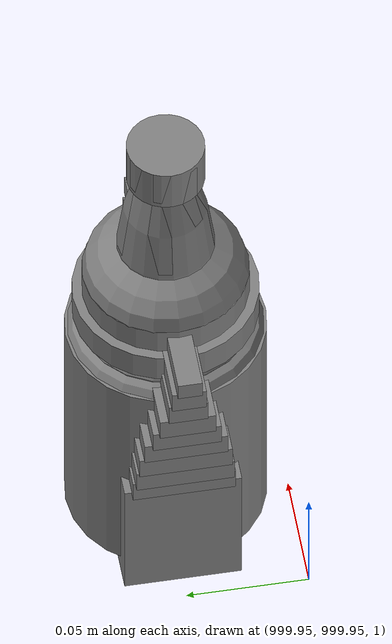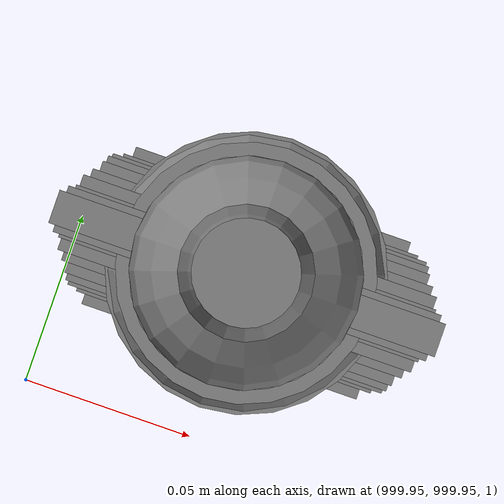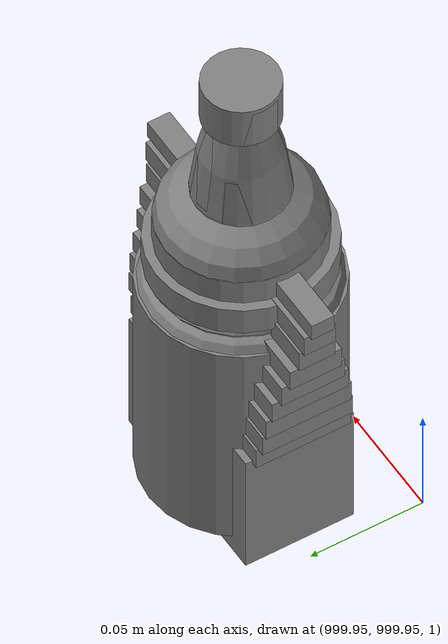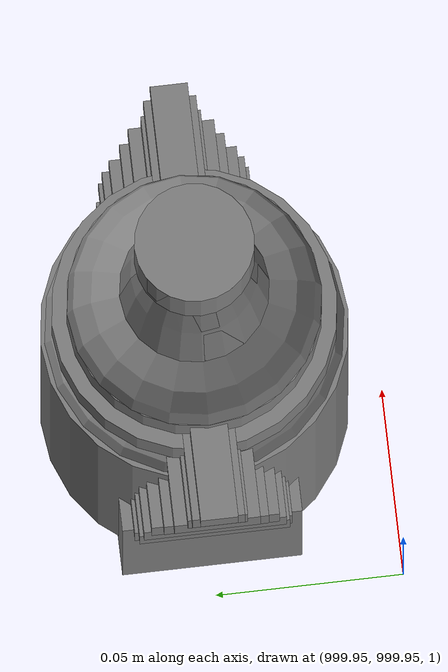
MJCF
<mujoco>
    <option gravity="0.000000000 0.000000000 -9.810000420" timestep="0.0166666" integrator="implicitfast" density="1.225" viscosity="1.8000001e-05" noslip_iterations="10" iterations="100" sdf_iterations="50">
        <flag multiccd="disable"/>
    </option>
    <size memory="1000M"/>
    <compiler coordinate="local"/>
    <worldbody>
        <light cutoff="30" pos="0 1 1" dir="0 -1 -2"/>
        <light cutoff="30" pos="0 -1 1" dir="0 1 -2"/>
        <body pos="0.000000000 0.000000000 0.000000000" euler="0.000000000 0.000000000 0.000000000" name=" Static Objects_ Static Objects">
            <geom contype="1" conaffinity="1" density="1000" type="box" material="" rgba="0.500000000 0.500000000 0.500000000 1.000000000" solimp="0.899999976 0.949999988 0.001000000" friction="1.000000000 0.005000000 0.000100000" solref="0.020000000 1.000000000" margin="0" condim="3" group="0" pos="-3.101639986 6.150595188 1.018643856" quat="1.000000000 0.000000000 0.000000000 0.000000000" size="0.050000001 0.579999983 1.019999981" name=" Static Objects_geom_EFA85E5D_9080_4509_9FFD_3915F3408B70"/>
            <geom contype="1" conaffinity="1" density="1000" type="box" material="" rgba="0.500000000 0.500000000 0.500000000 1.000000000" solimp="0.899999976 0.949999988 0.001000000" friction="1.000000000 0.005000000 0.000100000" solref="0.020000000 1.000000000" margin="0" condim="3" group="0" pos="-2.825197220 6.153595448 1.115278244" quat="0.707107067 0.000000000 0.000000000 0.707106471" size="0.550000012 0.239999995 0.025000000" name=" Static Objects_geom_082AA9F9_5E64_4BEF_A03A_7DEB397CEF4E"/>
            <geom contype="1" conaffinity="1" density="1000" type="box" material="" rgba="0.500000000 0.500000000 0.500000000 1.000000000" solimp="0.899999976 0.949999988 0.001000000" friction="1.000000000 0.005000000 0.000100000" solref="0.020000000 1.000000000" margin="0" condim="3" group="0" pos="-2.825197220 6.153595448 0.097434282" quat="0.707107067 0.000000000 0.000000000 0.707106471" size="0.550000012 0.239999995 0.098999999" name=" Static Objects_geom_77CFBB9A_7518_45A0_897B_281D22D3AFAF"/>
            <geom contype="1" conaffinity="1" density="1000" type="box" material="" rgba="0.500000000 0.500000000 0.500000000 1.000000000" solimp="0.899999976 0.949999988 0.001000000" friction="1.000000000 0.005000000 0.000100000" solref="0.020000000 1.000000000" margin="0" condim="3" group="0" pos="-6.293097973 6.153595448 1.114443064" quat="0.707107067 0.000000000 0.000000000 0.707106471" size="0.529999971 3.134999990 0.025000000" name=" Static Objects_geom_A7BDCE87_FAEC_4D77_BE04_1D99C83E5412"/>
            <geom contype="1" conaffinity="1" density="1000" type="box" material="" rgba="0.500000000 0.500000000 0.500000000 1.000000000" solimp="0.899999976 0.949999988 0.001000000" friction="1.000000000 0.005000000 0.000100000" solref="0.020000000 1.000000000" margin="0" condim="3" group="0" pos="-2.825197220 6.153595448 1.563861728" quat="0.707107067 0.000000000 0.000000000 0.707106471" size="0.550000012 0.239999995 0.025000000" name=" Static Objects_geom_9A9768C0_DED3_4240_9BF0_CF85D84E53C8"/>
            <geom contype="1" conaffinity="1" density="1000" type="box" material="" rgba="0.500000000 0.500000000 0.500000000 1.000000000" solimp="0.899999976 0.949999988 0.001000000" friction="1.000000000 0.005000000 0.000100000" solref="0.020000000 1.000000000" margin="0" condim="3" group="0" pos="-6.311686516 6.153595448 1.018643856" quat="0.707107067 0.000000000 0.000000000 0.707106471" size="0.050000001 3.150000095 1.019999981" name=" Static Objects_geom_846ABE68_8D47_43DA_9382_8D4F9C6F3763"/>
            <geom contype="1" conaffinity="1" density="1000" type="box" material="" rgba="0.500000000 0.500000000 0.500000000 1.000000000" solimp="0.899999976 0.949999988 0.001000000" friction="1.000000000 0.005000000 0.000100000" solref="0.020000000 1.000000000" margin="0" condim="3" group="0" pos="-6.286010742 6.153595448 0.096129179" quat="0.707107067 0.000000000 0.000000000 0.707106471" size="0.529999971 3.134999990 0.098999999" name=" Static Objects_geom_7BDD4106_2622_4315_A1C6_537571038CC4"/>
            <geom contype="1" conaffinity="1" density="1000" type="box" material="" rgba="0.500000000 0.500000000 0.500000000 1.000000000" solimp="0.899999976 0.949999988 0.001000000" friction="1.000000000 0.005000000 0.000100000" solref="0.020000000 1.000000000" margin="0" condim="3" group="0" pos="-2.825197220 6.153595448 0.629031777" quat="0.707107067 0.000000000 0.000000000 0.707106471" size="0.550000012 0.239999995 0.025000000" name=" Static Objects_geom_F64417EA_C36A_40C6_9F86_EBBCE067B4B6"/>
            <geom contype="1" conaffinity="1" density="1000" type="box" material="" rgba="0.500000000 0.500000000 0.500000000 1.000000000" solimp="0.899999976 0.949999988 0.001000000" friction="1.000000000 0.005000000 0.000100000" solref="0.020000000 1.000000000" margin="0" condim="3" group="0" pos="-6.286010742 6.153595448 1.563861728" quat="0.707107067 0.000000000 0.000000000 0.707106471" size="0.529999971 3.134999990 0.025000000" name=" Static Objects_geom_11860512_3FFE_453C_B7BB_CDD710D18579"/>
            <geom contype="1" conaffinity="1" density="1000" type="box" material="" rgba="0.500000000 0.500000000 0.500000000 1.000000000" solimp="0.899999976 0.949999988 0.001000000" friction="1.000000000 0.005000000 0.000100000" solref="0.020000000 1.000000000" margin="0" condim="3" group="0" pos="-6.286010742 6.153595448 0.629031777" quat="0.707107067 0.000000000 0.000000000 0.707106471" size="0.529999971 3.134999990 0.025000000" name=" Static Objects_geom_83256AA9_6C7B_4142_ACB8_C2C202187FA3"/>
            <geom contype="1" conaffinity="1" density="1000" type="box" material="" rgba="0.500000000 0.500000000 0.500000000 1.000000000" solimp="0.899999976 0.949999988 0.001000000" friction="1.000000000 0.005000000 0.000100000" solref="0.020000000 1.000000000" margin="0" condim="3" group="0" pos="-7.719123363 2.867671013 1.173410416" quat="1.000000000 0.000000000 0.000000000 0.000000000" size="0.250000000 0.250000000 0.079999998" name=" Static Objects_geom_A9E72DE1_AEA1_401D_93A6_569E675326E8"/>
            <geom contype="1" conaffinity="1" density="1000" type="box" material="" rgba="0.500000000 0.500000000 0.500000000 1.000000000" solimp="0.899999976 0.949999988 0.001000000" friction="1.000000000 0.005000000 0.000100000" solref="0.020000000 1.000000000" margin="0" condim="3" group="0" pos="-7.408766270 3.088089943 1.776644945" quat="0.928051054 0.000000000 0.000000000 0.372453064" size="0.050000001 0.100000001 0.050000001" name=" Static Objects_geom_C094CA2A_EF3D_403E_8D7A_9D78D783CE7C"/>
            <geom contype="1" conaffinity="1" density="1000" type="box" material="" rgba="0.500000000 0.500000000 0.500000000 1.000000000" solimp="0.899999976 0.949999988 0.001000000" friction="1.000000000 0.005000000 0.000100000" solref="0.020000000 1.000000000" margin="0" condim="3" group="0" pos="-7.719123363 2.958004713 1.530241251" quat="1.000000000 0.000000000 0.000000000 0.000000000" size="0.250000000 0.159999996 0.280000001" name=" Static Objects_geom_BE293E2C_A4DA_4C4E_8697_C7AC4102B555"/>
            <geom contype="1" conaffinity="1" density="1000" type="cylinder" material="" rgba="0.500000000 0.500000000 0.500000000 1.000000000" solimp="0.899999976 0.949999988 0.001000000" friction="1.000000000 0.005000000 0.000100000" solref="0.020000000 1.000000000" margin="0" condim="3" group="0" pos="-7.427312374 3.069516420 1.502544641" quat="0.928051054 0.000000000 0.000000000 0.372453064" size="0.015000000 0.230000004 0.100000001" name=" Static Objects_geom_456CAD23_74F4_4687_A1A9_EB17BA976807"/>
            <geom contype="1" conaffinity="1" density="1000" type="box" material="" rgba="0.500000000 0.500000000 0.500000000 1.000000000" solimp="0.899999976 0.949999988 0.001000000" friction="1.000000000 0.005000000 0.000100000" solref="0.020000000 1.000000000" margin="0" condim="3" group="0" pos="-7.437745571 3.067511320 1.289965630" quat="1.000000000 0.000000000 0.000000000 0.000000000" size="0.029999999 0.020000000 0.020000000" name=" Static Objects_geom_3F6E9EF3_CA72_4380_9D2F_A15F7A9DF909"/>
            <geom contype="1" conaffinity="1" density="1000" type="box" material="" rgba="0.500000000 0.500000000 0.500000000 1.000000000" solimp="0.899999976 0.949999988 0.001000000" friction="1.000000000 0.005000000 0.000100000" solref="0.020000000 1.000000000" margin="0" condim="3" group="0" pos="-9.058088303 6.434794426 1.209077358" quat="1.000000000 0.000000000 0.000000000 0.000000000" size="0.250000000 0.100000001 0.070000000" name=" Static Objects_geom_68EBB5A2_66BA_4AA6_A82C_A53595620F86"/>
            <geom contype="1" conaffinity="1" density="1000" type="box" material="" rgba="0.500000000 0.500000000 0.500000000 1.000000000" solimp="0.899999976 0.949999988 0.001000000" friction="1.000000000 0.005000000 0.000100000" solref="0.020000000 1.000000000" margin="0" condim="3" group="0" pos="-7.886891365 6.459744930 0.352518857" quat="1.000000000 0.000000000 0.000000000 0.000000000" size="1.500000000 0.200000003 0.150000006" name=" Static Objects_geom_98FECD14_1F58_4783_A373_15AAE81978BC"/>
            <geom contype="1" conaffinity="1" density="1000" type="box" material="" rgba="0.500000000 0.500000000 0.500000000 1.000000000" solimp="0.899999976 0.949999988 0.001000000" friction="1.000000000 0.005000000 0.000100000" solref="0.020000000 1.000000000" margin="0" condim="3" group="0" pos="-9.237723351 6.464855671 1.209077358" quat="1.000000000 0.000000000 0.000000000 0.000000000" size="0.100000001 0.100000001 0.070000000" name=" Static Objects_geom_6076B160_C717_447D_A6BE_AE9CADCE0C82"/>
            <geom contype="1" conaffinity="1" density="1000" type="box" material="" rgba="0.500000000 0.500000000 0.500000000 1.000000000" solimp="0.899999976 0.949999988 0.001000000" friction="1.000000000 0.005000000 0.000100000" solref="0.020000000 1.000000000" margin="0" condim="3" group="0" pos="-6.924745083 6.362090111 1.214329123" quat="1.000000000 0.000000000 0.000000000 0.000000000" size="0.200000003 0.100000001 0.075000003" name=" Static Objects_geom_219BD3DA_3194_4621_B427_135FCF060DCA"/>
            <geom contype="1" conaffinity="1" density="1000" type="box" material="" rgba="0.500000000 0.500000000 0.500000000 1.000000000" solimp="0.899999976 0.949999988 0.001000000" friction="1.000000000 0.005000000 0.000100000" solref="0.020000000 1.000000000" margin="0" condim="3" group="0" pos="-4.407354832 6.459744930 1.292199373" quat="1.000000000 0.000000000 0.000000000 0.000000000" size="1.240000010 0.200000003 0.150000006" name=" Static Objects_geom_53E0C645_0011_4008_BC88_9EC10E853C63"/>
            <geom contype="1" conaffinity="1" density="1000" type="box" material="" rgba="0.500000000 0.500000000 0.500000000 1.000000000" solimp="0.899999976 0.949999988 0.001000000" friction="1.000000000 0.005000000 0.000100000" solref="0.020000000 1.000000000" margin="0" condim="3" group="0" pos="-5.611940861 6.318420410 0.350975692" quat="1.000000000 0.000000000 0.000000000 0.000000000" size="0.699999988 0.100000001 0.150000006" name=" Static Objects_geom_D1A62004_06A0_41ED_A57E_9E2A587758B7"/>
            <geom contype="1" conaffinity="1" density="1000" type="box" material="" rgba="0.500000000 0.500000000 0.500000000 1.000000000" solimp="0.899999976 0.949999988 0.001000000" friction="1.000000000 0.005000000 0.000100000" solref="0.020000000 1.000000000" margin="0" condim="3" group="0" pos="-6.300771236 6.459744930 1.744376063" quat="1.000000000 0.000000000 0.000000000 0.000000000" size="3.000000000 0.200000003 0.150000006" name=" Static Objects_geom_46296127_F8D7_402D_AB4F_136CA298D374"/>
            <geom contype="1" conaffinity="1" density="1000" type="box" material="" rgba="0.500000000 0.500000000 0.500000000 1.000000000" solimp="0.899999976 0.949999988 0.001000000" friction="1.000000000 0.005000000 0.000100000" solref="0.020000000 1.000000000" margin="0" condim="3" group="0" pos="-8.844120979 6.464855671 1.209077358" quat="1.000000000 0.000000000 0.000000000 0.000000000" size="0.100000001 0.100000001 0.070000000" name=" Static Objects_geom_604E90FF_F3DE_4752_AF7F_974C8779F327"/>
            <geom contype="1" conaffinity="1" density="1000" type="box" material="" rgba="0.500000000 0.500000000 0.500000000 1.000000000" solimp="0.899999976 0.949999988 0.001000000" friction="1.000000000 0.005000000 0.000100000" solref="0.020000000 1.000000000" margin="0" condim="3" group="0" pos="-6.824534416 6.447464466 1.212718010" quat="1.000000000 0.000000000 0.000000000 0.000000000" size="0.100000001 0.100000001 0.075000003" name=" Static Objects_geom_AD3D7FB7_9BD0_402F_9CA2_D87DEEDF6AB7"/>
            <geom contype="1" conaffinity="1" density="1000" type="box" material="" rgba="0.500000000 0.500000000 0.500000000 1.000000000" solimp="0.899999976 0.949999988 0.001000000" friction="1.000000000 0.005000000 0.000100000" solref="0.020000000 1.000000000" margin="0" condim="3" group="0" pos="-6.751636982 6.459744930 0.800981164" quat="1.000000000 0.000000000 0.000000000 0.000000000" size="2.200000048 0.200000003 0.150000006" name=" Static Objects_geom_1E335994_D15D_484A_BF6C_FE19A6EC262F"/>
            <geom contype="1" conaffinity="1" density="1000" type="box" material="" rgba="0.500000000 0.500000000 0.500000000 1.000000000" solimp="0.899999976 0.949999988 0.001000000" friction="1.000000000 0.005000000 0.000100000" solref="0.020000000 1.000000000" margin="0" condim="3" group="0" pos="-6.098561764 6.327973843 1.292199373" quat="1.000000000 0.000000000 0.000000000 0.000000000" size="0.500000000 0.100000001 0.150000006" name=" Static Objects_geom_CDDEB1D7_200F_4B06_82D2_465B49C7973D"/>
            <geom contype="1" conaffinity="1" density="1000" type="box" material="" rgba="0.500000000 0.500000000 0.500000000 1.000000000" solimp="0.899999976 0.949999988 0.001000000" friction="1.000000000 0.005000000 0.000100000" solref="0.020000000 1.000000000" margin="0" condim="3" group="0" pos="-3.907610416 6.318625927 0.800981164" quat="1.000000000 0.000000000 0.000000000 0.000000000" size="0.500000000 0.100000001 0.150000006" name=" Static Objects_geom_26612D0C_1CC5_4830_9C26_B13C7B69248E"/>
            <geom contype="1" conaffinity="1" density="1000" type="box" material="" rgba="0.500000000 0.500000000 0.500000000 1.000000000" solimp="0.899999976 0.949999988 0.001000000" friction="1.000000000 0.005000000 0.000100000" solref="0.020000000 1.000000000" margin="0" condim="3" group="0" pos="-7.373087406 6.458900928 1.214329123" quat="1.000000000 0.000000000 0.000000000 0.000000000" size="0.250000000 0.200000003 0.075000003" name=" Static Objects_geom_C86E1D9A_C9B0_45BC_A8D4_B4C235BAB376"/>
            <geom contype="1" conaffinity="1" density="1000" type="box" material="" rgba="0.500000000 0.500000000 0.500000000 1.000000000" solimp="0.899999976 0.949999988 0.001000000" friction="1.000000000 0.005000000 0.000100000" solref="0.020000000 1.000000000" margin="0" condim="3" group="0" pos="-4.035642624 6.459744930 0.352518857" quat="1.000000000 0.000000000 0.000000000 0.000000000" size="0.800000012 0.200000003 0.150000006" name=" Static Objects_geom_1235F098_6E10_4F89_9849_309F5B083B3B"/>
            <geom contype="1" conaffinity="1" density="1000" type="box" material="" rgba="0.500000000 0.500000000 0.500000000 1.000000000" solimp="0.899999976 0.949999988 0.001000000" friction="1.000000000 0.005000000 0.000100000" solref="0.020000000 1.000000000" margin="0" condim="3" group="0" pos="-6.460197449 2.937205315 0.548931718" quat="1.000000000 0.000000000 0.000000000 0.000000000" size="2.650000095 0.430000007 0.550000012" name=" Static Objects_geom_CED5D6E2_F152_4752_A6E4_EFBD1D87471B"/>
            <geom contype="1" conaffinity="1" density="1000" type="box" material="" rgba="0.500000000 0.500000000 0.500000000 1.000000000" solimp="0.899999976 0.949999988 0.001000000" friction="1.000000000 0.005000000 0.000100000" solref="0.020000000 1.000000000" margin="0" condim="3" group="0" pos="-4.240264893 1.327049494 0.549888909" quat="1.000000000 0.000000000 0.000000000 0.000000000" size="0.430000007 1.200000048 0.550000012" name=" Static Objects_geom_4595D422_18EC_41E3_A231_76F437A752D7"/>
            <geom contype="1" conaffinity="1" density="1000" type="box" material="" rgba="0.500000000 0.500000000 0.500000000 1.000000000" solimp="0.899999976 0.949999988 0.001000000" friction="1.000000000 0.005000000 0.000100000" solref="0.020000000 1.000000000" margin="0" condim="3" group="0" pos="-8.830721855 2.096410990 0.549305558" quat="1.000000000 0.000000000 0.000000000 0.000000000" size="0.280000001 0.430000007 0.550000012" name=" Static Objects_geom_4A63FA07_DC09_4A66_AEFC_2F9F9AE6B2A1"/>
            <geom contype="1" conaffinity="1" density="1000" type="plane" material="" rgba="0.500000000 0.500000000 0.500000000 1.000000000" solimp="0.899999976 0.949999988 0.001000000" friction="1.000000000 0.005000000 0.000100000" solref="0.020000000 1.000000000" margin="0" condim="3" group="0" pos="-6.000000000 10.399999619 0.000000000" quat="1.000000000 0.000000000 0.000000000 0.000000000" size="6.050000191 10.800000191 0.010000000" name=" Static Objects_geom_92468EF1_E8D4_41E7_96EE_97F2F1DB0B4E"/>
            <geom contype="1" conaffinity="1" density="1000" type="box" material="" rgba="0.500000000 0.500000000 0.500000000 1.000000000" solimp="0.899999976 0.949999988 0.001000000" friction="1.000000000 0.005000000 0.000100000" solref="0.020000000 1.000000000" margin="0" condim="3" group="0" pos="-6.000000000 0.035000000 2.000000000" quat="1.000000000 0.000000000 0.000000000 0.000000000" size="6.079999924 0.070000000 2.000000000" name=" Static Objects_geom_C815988E_36AC_42F8_BB15_E8E155205C39"/>
            <geom contype="1" conaffinity="1" density="1000" type="box" material="" rgba="0.500000000 0.500000000 0.500000000 1.000000000" solimp="0.899999976 0.949999988 0.001000000" friction="1.000000000 0.005000000 0.000100000" solref="0.020000000 1.000000000" margin="0" condim="3" group="0" pos="-6.000000000 20.159999847 2.000000000" quat="1.000000000 0.000000000 0.000000000 0.000000000" size="6.079999924 0.070000000 2.000000000" name=" Static Objects_geom_47EAD18D_3A0E_4177_B3ED_8936DEA71132"/>
            <geom contype="1" conaffinity="1" density="1000" type="box" material="" rgba="0.500000000 0.500000000 0.500000000 1.000000000" solimp="0.899999976 0.949999988 0.001000000" friction="1.000000000 0.005000000 0.000100000" solref="0.020000000 1.000000000" margin="0" condim="3" group="0" pos="0.000000000 10.000000000 2.000000000" quat="1.000000000 0.000000000 0.000000000 0.000000000" size="0.070000000 10.500000000 2.000000000" name=" Static Objects_geom_1EF55019_7C95_45FC_AA1D_CE92D08741A6"/>
            <geom contype="1" conaffinity="1" density="1000" type="box" material="" rgba="0.500000000 0.500000000 0.500000000 1.000000000" solimp="0.899999976 0.949999988 0.001000000" friction="1.000000000 0.005000000 0.000100000" solref="0.020000000 1.000000000" margin="0" condim="3" group="0" pos="-12.050000191 10.000000000 2.000000000" quat="1.000000000 0.000000000 0.000000000 0.000000000" size="0.070000000 10.500000000 2.000000000" name=" Static Objects_geom_8DBDE29F_0118_48D3_83D4_1E5DF6200730"/>
        </body>
        <body pos="1000.000000000 1000.000000000 1.000000000" euler="0.000000000 0.000000000 0.000000000" name="openloong_gripper_2f85_fix_base_usda_salt">
            <geom contype="1" conaffinity="1" density="1000" type="box" material="" rgba="0.500000000 0.500000000 0.500000000 1.000000000" solimp="0.899999976 0.949999988 0.001000000" friction="1.000000000 0.005000000 0.000100000" solref="0.020000000 1.000000000" margin="0" condim="3" group="0" pos="0.000305176 0.000000000 0.084862232" quat="1.000000000 0.000000000 0.000000000 0.000000000" size="0.048999999 0.018999999 0.005000000" name="openloong_gripper_2f85_fix_base_usda_geom_B2B74E1D_5D2D_4363_9394_DA1E928B1E90"/>
            <geom contype="1" conaffinity="1" density="1000" type="box" material="" rgba="0.500000000 0.500000000 0.500000000 1.000000000" solimp="0.899999976 0.949999988 0.001000000" friction="1.000000000 0.005000000 0.000100000" solref="0.020000000 1.000000000" margin="0" condim="3" group="0" pos="0.000305176 0.000000000 0.104564309" quat="1.000000000 0.000000000 0.000000000 0.000000000" size="0.052000001 0.014000000 0.005000000" name="openloong_gripper_2f85_fix_base_usda_geom_87C6F031_A1A9_46F6_885D_332E28C0DC01"/>
            <geom contype="1" conaffinity="1" density="1000" type="box" material="" rgba="0.500000000 0.500000000 0.500000000 1.000000000" solimp="0.899999976 0.949999988 0.001000000" friction="1.000000000 0.005000000 0.000100000" solref="0.020000000 1.000000000" margin="0" condim="3" group="0" pos="0.000305176 0.000000000 0.114487171" quat="1.000000000 0.000000000 0.000000000 0.000000000" size="0.054000001 0.011500000 0.005000000" name="openloong_gripper_2f85_fix_base_usda_geom_C2AC7814_9408_42E9_9690_6200118FE252"/>
            <geom contype="1" conaffinity="1" density="1000" type="box" material="" rgba="0.500000000 0.500000000 0.500000000 1.000000000" solimp="0.899999976 0.949999988 0.001000000" friction="1.000000000 0.005000000 0.000100000" solref="0.020000000 1.000000000" margin="0" condim="3" group="0" pos="0.000305176 0.000000000 0.075103164" quat="1.000000000 0.000000000 0.000000000 0.000000000" size="0.048000000 0.020000000 0.005000000" name="openloong_gripper_2f85_fix_base_usda_geom_EB775EB3_0913_4F42_A228_529F257F7024"/>
            <geom contype="1" conaffinity="1" density="1000" type="box" material="" rgba="0.500000000 0.500000000 0.500000000 1.000000000" solimp="0.899999976 0.949999988 0.001000000" friction="1.000000000 0.005000000 0.000100000" solref="0.020000000 1.000000000" margin="0" condim="3" group="0" pos="0.000305176 0.000000000 0.134892464" quat="1.000000000 0.000000000 0.000000000 0.000000000" size="0.057000000 0.007000000 0.005000000" name="openloong_gripper_2f85_fix_base_usda_geom_852ED9B8_2E9F_4872_B324_96D27027CDC6"/>
            <geom contype="1" conaffinity="1" density="1000" type="box" material="" rgba="0.500000000 0.500000000 0.500000000 1.000000000" solimp="0.899999976 0.949999988 0.001000000" friction="1.000000000 0.005000000 0.000100000" solref="0.020000000 1.000000000" margin="0" condim="3" group="0" pos="0.000305176 0.000000000 0.094920278" quat="1.000000000 0.000000000 0.000000000 0.000000000" size="0.050000001 0.017000001 0.005000000" name="openloong_gripper_2f85_fix_base_usda_geom_BA2C5490_D298_407B_A4F3_D9502CF0D058"/>
            <geom contype="1" conaffinity="1" density="1000" type="box" material="" rgba="0.500000000 0.500000000 0.500000000 1.000000000" solimp="0.899999976 0.949999988 0.001000000" friction="1.000000000 0.005000000 0.000100000" solref="0.020000000 1.000000000" margin="0" condim="3" group="0" pos="0.000305176 0.000000000 0.065204859" quat="1.000000000 0.000000000 0.000000000 0.000000000" size="0.045000002 0.021000000 0.005000000" name="openloong_gripper_2f85_fix_base_usda_geom_95A5423A_7F6C_44FD_8DA0_EFBAB749C64C"/>
            <geom contype="1" conaffinity="1" density="1000" type="box" material="" rgba="0.500000000 0.500000000 0.500000000 1.000000000" solimp="0.899999976 0.949999988 0.001000000" friction="1.000000000 0.005000000 0.000100000" solref="0.020000000 1.000000000" margin="0" condim="3" group="0" pos="0.000305176 0.000000000 0.144135714" quat="1.000000000 0.000000000 0.000000000 0.000000000" size="0.059000000 0.005000000 0.004000000" name="openloong_gripper_2f85_fix_base_usda_geom_BA5CA399_4940_4165_B9A5_DACFB2E19BA7"/>
            <geom contype="1" conaffinity="1" density="1000" type="box" material="" rgba="0.500000000 0.500000000 0.500000000 1.000000000" solimp="0.899999976 0.949999988 0.001000000" friction="1.000000000 0.005000000 0.000100000" solref="0.020000000 1.000000000" margin="0" condim="3" group="0" pos="0.000000000 0.000000000 0.031593561" quat="1.000000000 0.000000000 0.000000000 0.000000000" size="0.041999999 0.024000000 0.029999999" name="openloong_gripper_2f85_fix_base_usda_geom_5E896D3C_B8B6_4CF3_A8C8_98300CA52766"/>
            <geom contype="1" conaffinity="1" density="1000" type="box" material="" rgba="0.500000000 0.500000000 0.500000000 1.000000000" solimp="0.899999976 0.949999988 0.001000000" friction="1.000000000 0.005000000 0.000100000" solref="0.020000000 1.000000000" margin="0" condim="3" group="0" pos="0.000305176 0.000000000 0.124608755" quat="1.000000000 0.000000000 0.000000000 0.000000000" size="0.055000000 0.008000000 0.005000000" name="openloong_gripper_2f85_fix_base_usda_geom_08CA963F_8999_496B_AD3C_B6A06E1FDDC6"/>
            <freejoint name="openloong_gripper_2f85_fix_base_usda_salt_joint"/>
            <site size="0.005000000 0.005000000 0.005000000" rgba="0.500000000 0.500000000 0.500000000 1.000000000" pos="0.000000000 0.000000000 0.000000000" quat="1.000000000 0.000000000 0.000000000 0.000000000" group="0" type="sphere" name="openloong_gripper_2f85_fix_base_usda_saltsite"/>
        </body>
        <body pos="-2.181739092 5.979894161 1.798121810" euler="-49.125087738 35.111591339 -152.224822998" mocap="true" name="spotlight1_SpotLight"/>
        <body pos="-2.301926613 5.982351780 1.725652575" euler="73.087501526 54.375308990 -155.807556152" mocap="true" name="spotlight6_SpotLight"/>
        <body pos="1000.000000000 1000.000000000 1.000000000" euler="0.000000000 0.000000000 0.000000000" name="openloong_gripper_2f85_fix_base_usda_bottle_blue">
            <geom contype="1" conaffinity="1" density="1000" type="ellipsoid" material="" rgba="0.500000000 0.500000000 0.500000000 1.000000000" solimp="0.899999976 0.949999988 0.001000000" friction="1.000000000 0.005000000 0.000100000" solref="0.020000000 1.000000000" margin="0" condim="3" group="0" pos="0.000000000 0.000000000 0.118920922" quat="1.000000000 0.000000000 0.000000000 0.000000000" size="0.030999999 0.030999999 0.029999999" name="openloong_gripper_2f85_fix_base_usda_geom_5C293FA3_8EEA_40B8_B26E_7A93ACA5E5BF"/>
            <geom contype="1" conaffinity="1" density="1000" type="box" material="" rgba="0.500000000 0.500000000 0.500000000 1.000000000" solimp="0.899999976 0.949999988 0.001000000" friction="1.000000000 0.005000000 0.000100000" solref="0.020000000 1.000000000" margin="0" condim="3" group="0" pos="0.000000000 0.000000000 0.002164602" quat="1.000000000 0.000000000 0.000000000 0.000000000" size="0.020000000 0.020000000 0.003000000" name="openloong_gripper_2f85_fix_base_usda_geom_73DCA677_B3F7_4F3E_A54B_87A2220A6C4D"/>
            <geom contype="1" conaffinity="1" density="1000" type="cylinder" material="" rgba="0.500000000 0.500000000 0.500000000 1.000000000" solimp="0.899999976 0.949999988 0.001000000" friction="1.000000000 0.005000000 0.000100000" solref="0.020000000 1.000000000" margin="0" condim="3" group="0" pos="0.000000000 -0.000366211 0.060859680" quat="1.000000000 0.000000000 0.000000000 0.000000000" size="0.030999999 0.057999998 1.000000000" name="openloong_gripper_2f85_fix_base_usda_geom_890C0035_C7FB_4C38_AB9C_02CE68145E95"/>
            <geom contype="1" conaffinity="1" density="1000" type="cylinder" material="" rgba="0.500000000 0.500000000 0.500000000 1.000000000" solimp="0.899999976 0.949999988 0.001000000" friction="1.000000000 0.005000000 0.000100000" solref="0.020000000 1.000000000" margin="0" condim="3" group="0" pos="0.000000000 0.000000000 0.220594406" quat="1.000000000 0.000000000 0.000000000 0.000000000" size="0.016000001 0.010000000 1.000000000" name="openloong_gripper_2f85_fix_base_usda_geom_83E23E7C_C51D_4809_A955_200ED66B32ED"/>
            <geom contype="1" conaffinity="1" density="1000" type="ellipsoid" material="" rgba="0.500000000 0.500000000 0.500000000 1.000000000" solimp="0.899999976 0.949999988 0.001000000" friction="1.000000000 0.005000000 0.000100000" solref="0.020000000 1.000000000" margin="0" condim="3" group="0" pos="0.000000000 0.000000000 0.144259930" quat="1.000000000 0.000000000 0.000000000 0.000000000" size="0.021000000 0.021000000 0.079999998" name="openloong_gripper_2f85_fix_base_usda_geom_2A0A5563_EA8B_4E00_AE8C_E2D704BB2004"/>
            <freejoint name="openloong_gripper_2f85_fix_base_usda_bottle_blue_joint"/>
            <site size="0.005000000 0.005000000 0.005000000" rgba="0.500000000 0.500000000 0.500000000 1.000000000" pos="0.000000000 0.000000000 0.000000000" quat="0.999961913 0.008726535 0.000000000 0.000000000" group="0" type="sphere" name="openloong_gripper_2f85_fix_base_usda_bottle_bluesite"/>
        </body>
        <body pos="1000.000000000 1000.000000000 1.000000000" euler="0.000000000 0.000000000 0.000000000" name="openloong_gripper_2f85_fix_base_usda_jar_01">
            <geom contype="1" conaffinity="1" density="1000" type="box" material="" rgba="0.500000000 0.500000000 0.500000000 1.000000000" solimp="0.899999976 0.949999988 0.001000000" friction="1.000000000 0.005000000 0.000100000" solref="0.020000000 1.000000000" margin="0" condim="3" group="0" pos="0.000000000 0.000000000 0.006158113" quat="1.000000000 0.000000000 0.000000000 0.000000000" size="0.020000000 0.020000000 0.005000000" name="openloong_gripper_2f85_fix_base_usda_geom_FA3882E7_94F2_459F_8182_C667D682081A"/>
            <geom contype="1" conaffinity="1" density="1000" type="cylinder" material="" rgba="0.500000000 0.500000000 0.500000000 1.000000000" solimp="0.899999976 0.949999988 0.001000000" friction="1.000000000 0.005000000 0.000100000" solref="0.020000000 1.000000000" margin="0" condim="3" group="0" pos="0.000000000 0.000000000 0.062744498" quat="1.000000000 0.000000000 0.000000000 0.000000000" size="0.041000001 0.052999999 1.000000000" name="openloong_gripper_2f85_fix_base_usda_geom_5AD7FB23_F533_4E72_8BEE_55A3A38DD7F5"/>
            <geom contype="1" conaffinity="1" density="1000" type="ellipsoid" material="" rgba="0.500000000 0.500000000 0.500000000 1.000000000" solimp="0.899999976 0.949999988 0.001000000" friction="1.000000000 0.005000000 0.000100000" solref="0.020000000 1.000000000" margin="0" condim="3" group="0" pos="0.000000000 0.000000000 0.122252703" quat="1.000000000 0.000000000 0.000000000 0.000000000" size="0.035999998 0.035999998 0.010000000" name="openloong_gripper_2f85_fix_base_usda_geom_0761E706_71D6_4C08_8599_52A9EAC63B0A"/>
            <geom contype="1" conaffinity="1" density="1000" type="cylinder" material="" rgba="0.500000000 0.500000000 0.500000000 1.000000000" solimp="0.899999976 0.949999988 0.001000000" friction="1.000000000 0.005000000 0.000100000" solref="0.020000000 1.000000000" margin="0" condim="3" group="0" pos="0.000000000 0.000000000 0.015747190" quat="1.000000000 0.000000000 0.000000000 0.000000000" size="0.035000000 0.010000000 1.000000000" name="openloong_gripper_2f85_fix_base_usda_geom_BBFEDEB9_48B2_47A1_A952_6464804F3C1E"/>
            <geom contype="1" conaffinity="1" density="1000" type="ellipsoid" material="" rgba="0.500000000 0.500000000 0.500000000 1.000000000" solimp="0.899999976 0.949999988 0.001000000" friction="1.000000000 0.005000000 0.000100000" solref="0.020000000 1.000000000" margin="0" condim="3" group="0" pos="0.000000000 0.000000000 0.115815401" quat="1.000000000 0.000000000 0.000000000 0.000000000" size="0.039999999 0.039999999 0.010000000" name="openloong_gripper_2f85_fix_base_usda_geom_64276C0A_B927_404C_A831_D72850A607E0"/>
            <geom contype="1" conaffinity="1" density="1000" type="cylinder" material="" rgba="0.500000000 0.500000000 0.500000000 1.000000000" solimp="0.899999976 0.949999988 0.001000000" friction="1.000000000 0.005000000 0.000100000" solref="0.020000000 1.000000000" margin="0" condim="3" group="0" pos="0.000000000 0.000000000 0.133183479" quat="1.000000000 0.000000000 0.000000000 0.000000000" size="0.037999999 0.006500000 1.000000000" name="openloong_gripper_2f85_fix_base_usda_geom_58CF8E31_0339_476B_869C_FC2BB9CCF531"/>
            <freejoint name="openloong_gripper_2f85_fix_base_usda_jar_01_joint"/>
            <site size="0.005000000 0.005000000 0.005000000" rgba="0.500000000 0.500000000 0.500000000 1.000000000" pos="0.000000000 0.000000000 0.000000000" quat="1.000000000 0.000000000 0.000000000 0.000000000" group="0" type="sphere" name="openloong_gripper_2f85_fix_base_usda_jar_01site"/>
        </body>
        <body pos="1000.000000000 1000.000000000 1.000000000" euler="0.000000000 0.000000000 0.000000000" name="openloong_gripper_2f85_fix_base_usda_can">
            <geom contype="1" conaffinity="1" density="1000" type="cylinder" material="" rgba="0.500000000 0.500000000 0.500000000 1.000000000" solimp="0.899999976 0.949999988 0.001000000" friction="1.000000000 0.005000000 0.000100000" solref="0.020000000 1.000000000" margin="0" condim="3" group="0" pos="0.000000000 0.000000000 0.079676986" quat="1.000000000 0.000000000 0.000000000 0.000000000" size="0.034000002 0.071999997 1.000000000" name="openloong_gripper_2f85_fix_base_usda_geom_F4D3941F_9F04_4CCE_9161_48EA366A2216"/>
            <geom contype="1" conaffinity="1" density="1000" type="ellipsoid" material="" rgba="0.500000000 0.500000000 0.500000000 1.000000000" solimp="0.899999976 0.949999988 0.001000000" friction="1.000000000 0.005000000 0.000100000" solref="0.020000000 1.000000000" margin="0" condim="3" group="0" pos="0.000000000 0.000000000 0.151854277" quat="1.000000000 0.000000000 0.000000000 0.000000000" size="0.034000002 0.034000002 0.020000000" name="openloong_gripper_2f85_fix_base_usda_geom_D9A9C3AC_7CFF_4662_97F8_4211B46BCEC6"/>
            <geom contype="1" conaffinity="1" density="1000" type="box" material="" rgba="0.500000000 0.500000000 0.500000000 1.000000000" solimp="0.899999976 0.949999988 0.001000000" friction="1.000000000 0.005000000 0.000100000" solref="0.020000000 1.000000000" margin="0" condim="3" group="0" pos="0.000000000 0.000000000 0.004777670" quat="1.000000000 0.000000000 0.000000000 0.000000000" size="0.020000000 0.020000000 0.005000000" name="openloong_gripper_2f85_fix_base_usda_geom_A5A9AC42_C6FC_4441_A0FB_740D985E57BF"/>
            <freejoint name="openloong_gripper_2f85_fix_base_usda_can_joint"/>
            <site size="0.005000000 0.005000000 0.005000000" rgba="0.500000000 0.500000000 0.500000000 1.000000000" pos="0.000000000 0.000000000 0.000000000" quat="1.000000000 0.000000000 0.000000000 0.000000000" group="0" type="sphere" name="openloong_gripper_2f85_fix_base_usda_cansite"/>
        </body>
        <body pos="-2.237253189 6.263741970 1.815459013" euler="-132.772155762 66.425613403 75.222740173" mocap="true" name="spotlight5_SpotLight"/>
        <body pos="1000.000000000 1000.000000000 1.000000000" euler="0.000000000 0.000000000 0.000000000" name="openloong_gripper_2f85_fix_base_usda_bottle_red">
            <geom contype="1" conaffinity="1" density="1000" type="ellipsoid" material="" rgba="0.500000000 0.500000000 0.500000000 1.000000000" solimp="0.899999976 0.949999988 0.001000000" friction="1.000000000 0.005000000 0.000100000" solref="0.020000000 1.000000000" margin="0" condim="3" group="0" pos="0.000000000 0.000000000 0.144284487" quat="1.000000000 0.000000000 0.000000000 0.000000000" size="0.021000000 0.021000000 0.079999998" name="openloong_gripper_2f85_fix_base_usda_geom_304D413A_977D_4853_A987_675BC008B667"/>
            <geom contype="1" conaffinity="1" density="1000" type="cylinder" material="" rgba="0.500000000 0.500000000 0.500000000 1.000000000" solimp="0.899999976 0.949999988 0.001000000" friction="1.000000000 0.005000000 0.000100000" solref="0.020000000 1.000000000" margin="0" condim="3" group="0" pos="0.000000000 0.000000000 0.220618963" quat="1.000000000 0.000000000 0.000000000 0.000000000" size="0.016000001 0.010000000 1.000000000" name="openloong_gripper_2f85_fix_base_usda_geom_6C5830CE_BFB5_4C07_A28C_FFDB1394AEA2"/>
            <geom contype="1" conaffinity="1" density="1000" type="ellipsoid" material="" rgba="0.500000000 0.500000000 0.500000000 1.000000000" solimp="0.899999976 0.949999988 0.001000000" friction="1.000000000 0.005000000 0.000100000" solref="0.020000000 1.000000000" margin="0" condim="3" group="0" pos="0.000000000 0.000000000 0.118945479" quat="1.000000000 0.000000000 0.000000000 0.000000000" size="0.030999999 0.030999999 0.029999999" name="openloong_gripper_2f85_fix_base_usda_geom_0224DAC7_CFD8_4217_A88D_2F000B33F9D3"/>
            <geom contype="1" conaffinity="1" density="1000" type="box" material="" rgba="0.500000000 0.500000000 0.500000000 1.000000000" solimp="0.899999976 0.949999988 0.001000000" friction="1.000000000 0.005000000 0.000100000" solref="0.020000000 1.000000000" margin="0" condim="3" group="0" pos="0.000000000 0.000000000 0.002189159" quat="1.000000000 0.000000000 0.000000000 0.000000000" size="0.020000000 0.020000000 0.003000000" name="openloong_gripper_2f85_fix_base_usda_geom_403DFDC9_9385_4CFD_94F4_9907004EE2FE"/>
            <geom contype="1" conaffinity="1" density="1000" type="cylinder" material="" rgba="0.500000000 0.500000000 0.500000000 1.000000000" solimp="0.899999976 0.949999988 0.001000000" friction="1.000000000 0.005000000 0.000100000" solref="0.020000000 1.000000000" margin="0" condim="3" group="0" pos="0.000000000 -0.000366211 0.060884237" quat="1.000000000 0.000000000 0.000000000 0.000000000" size="0.030999999 0.057999998 1.000000000" name="openloong_gripper_2f85_fix_base_usda_geom_62F245F2_692A_480E_AB19_921C3E920C3E"/>
            <freejoint name="openloong_gripper_2f85_fix_base_usda_bottle_red_joint"/>
            <site size="0.005000000 0.005000000 0.005000000" rgba="0.500000000 0.500000000 0.500000000 1.000000000" pos="0.000000000 0.000000000 0.000000000" quat="0.999961913 0.008726535 0.000000000 0.000000000" group="0" type="sphere" name="openloong_gripper_2f85_fix_base_usda_bottle_redsite"/>
        </body>
        <body pos="0.000000000 0.000000000 0.000000000" euler="0.000000000 0.000000000 0.000000000" name="Interactive Objects_Interactive Objects"/>
        <body pos="-3.510578632 3.403555870 -0.000000100" euler="0.000000000 0.000000000 40.200675964" name="openloong_gripper_2f85_fix_base_usda_PZ">
            <geom contype="1" conaffinity="1" density="1000" type="box" material="" rgba="0.500000000 0.500000000 0.500000000 1.000000000" solimp="0.899999976 0.949999988 0.001000000" friction="1.000000000 0.005000000 0.000100000" solref="0.020000000 1.000000000" margin="0" condim="3" group="0" pos="-0.047453165 0.056484699 0.373715430" quat="0.934750080 0.077914521 0.028795123 0.345459938" size="0.180000007 0.010000000 0.379999995" name="openloong_gripper_2f85_fix_base_usda_geom_3809DDF3_C34A_4C1A_8627_28E220F65569"/>
            <geom contype="1" conaffinity="1" density="1000" type="box" material="" rgba="0.500000000 0.500000000 0.500000000 1.000000000" solimp="0.899999976 0.949999988 0.001000000" friction="1.000000000 0.005000000 0.000100000" solref="0.020000000 1.000000000" margin="0" condim="3" group="0" pos="0.047452450 -0.054376602 0.374072611" quat="0.934387863 -0.082143910 -0.030358355 0.345326364" size="0.180000007 0.010000000 0.379999995" name="openloong_gripper_2f85_fix_base_usda_geom_7D907256_7F08_4717_8264_18612250F73B"/>
            <freejoint name="openloong_gripper_2f85_fix_base_usda_PZ"/>
        </body>
        <body pos="-6.332345009 2.779978037 1.034067392" euler="0.000000000 0.000000000 0.000000000" name="openloong_gripper_2f85_fix_base_usda_basket">
            <geom contype="1" conaffinity="1" density="100000" type="box" material="" rgba="0.500000000 0.500000000 0.500000000 1.000000000" solimp="0.899999976 0.949999988 0.001000000" friction="1.000000000 0.899999976 0.000100000" solref="0.020000000 1.000000000" margin="0" condim="3" group="0" pos="-0.172339439 0.000000000 0.168361664" quat="0.706172407 -0.036353018 -0.036353093 0.706170976" size="0.200000003 0.006000000 0.108000003" name="openloong_gripper_2f85_fix_base_usda_geom_C872FA35_E55E_44B2_A02D_7BE22BA9FBD4"/>
            <geom contype="1" conaffinity="1" density="100000" type="box" material="" rgba="0.500000000 0.500000000 0.500000000 1.000000000" solimp="0.899999976 0.949999988 0.001000000" friction="1.000000000 0.899999976 0.000100000" solref="0.020000000 1.000000000" margin="0" condim="3" group="0" pos="-0.039724827 -0.188568115 0.167089701" quat="0.997537494 0.070135131 0.000000000 0.000000000" size="0.150000006 0.006000000 0.108000003" name="openloong_gripper_2f85_fix_base_usda_geom_74EACAED_B4CB_4759_90C9_3B1FB9794F49"/>
            <geom contype="1" conaffinity="1" density="100000" type="box" material="" rgba="0.500000000 0.500000000 0.500000000 1.000000000" solimp="0.899999976 0.949999988 0.001000000" friction="1.000000000 0.899999976 0.000100000" solref="0.020000000 1.000000000" margin="0" condim="3" group="0" pos="-0.039724827 0.188377380 0.167089701" quat="0.997489929 -0.070808925 0.000000000 0.000000000" size="0.150000006 0.006000000 0.108000003" name="openloong_gripper_2f85_fix_base_usda_geom_48415C22_5707_42C3_8B1D_657ABCE36007"/>
            <geom contype="1" conaffinity="1" density="100000" type="box" material="" rgba="0.500000000 0.500000000 0.500000000 1.000000000" solimp="0.899999976 0.949999988 0.001000000" friction="1.000000000 0.899999976 0.000100000" solref="0.020000000 1.000000000" margin="0" condim="3" group="0" pos="-0.039724827 0.000000000 0.068126202" quat="1.000000000 0.000000000 0.000000000 0.000000000" size="0.129999995 0.174999997 0.006000000" name="openloong_gripper_2f85_fix_base_usda_geom_7354F883_0433_43F3_B152_8F3C0534C8E2"/>
            <geom contype="1" conaffinity="1" density="100000" type="box" material="" rgba="0.500000000 0.500000000 0.500000000 1.000000000" solimp="0.899999976 0.949999988 0.001000000" friction="1.000000000 0.899999976 0.000100000" solref="0.020000000 1.000000000" margin="0" condim="3" group="0" pos="0.094372749 0.000000000 0.168361664" quat="0.706172049 0.036353335 0.036353379 0.706171215" size="0.200000003 0.006000000 0.108000003" name="openloong_gripper_2f85_fix_base_usda_geom_C3C0CE03_2AA7_4A00_B378_D110F0FD40A3"/>
            <freejoint name="openloong_gripper_2f85_fix_base_usda_basket_joint"/>
            <site size="0.005000000 0.005000000 0.005000000" rgba="0.500000000 0.500000000 0.500000000 1.000000000" pos="0.000000000 0.000000000 0.000000000" quat="1.000000000 0.000000000 0.000000000 0.000000000" group="0" type="sphere" name="openloong_gripper_2f85_fix_base_usda_basketsite"/>
        </body>
        <body pos="-7.168000221 2.823999882 1.227496982" euler="-0.283413976 0.056829724 -0.133293271" name="openloong_gripper_2f85_fix_base_usda_Pos">
            <geom contype="1" conaffinity="1" density="1000" type="box" material="" rgba="0.500000000 0.500000000 0.500000000 1.000000000" solimp="0.899999976 0.949999988 0.001000000" friction="1.000000000 0.005000000 0.000100000" solref="0.020000000 1.000000000" margin="0" condim="3" group="0" pos="-0.002278805 0.074524641 -0.004134059" quat="0.315989345 0.948763072 -0.000000000 0.000000000" size="0.059999999 0.013000000 0.035000000" name="openloong_gripper_2f85_fix_base_usda_geom_660BB308_98C4_4DAD_98FE_C55E30581DB6"/>
            <geom contype="1" conaffinity="1" density="1000" type="box" material="" rgba="0.500000000 0.500000000 0.500000000 1.000000000" solimp="0.899999976 0.949999988 0.001000000" friction="1.000000000 0.005000000 0.000100000" solref="0.020000000 1.000000000" margin="0" condim="3" group="0" pos="-0.002278805 0.078031301 0.008128285" quat="0.990447521 -0.137893379 -0.000000000 -0.000000000" size="0.059999999 0.010000000 0.035000000" name="openloong_gripper_2f85_fix_base_usda_geom_0435AB37_DCD8_4276_83D5_CF4F38AA9D78"/>
            <geom contype="1" conaffinity="1" density="1000" type="box" material="" rgba="0.500000000 0.500000000 0.500000000 1.000000000" solimp="0.899999976 0.949999988 0.001000000" friction="1.000000000 0.005000000 0.000100000" solref="0.020000000 1.000000000" margin="0" condim="3" group="0" pos="-0.002278805 0.080785275 -0.002596974" quat="0.287325472 -0.957833409 0.000000000 -0.000000000" size="0.059999999 0.013000000 0.035000000" name="openloong_gripper_2f85_fix_base_usda_geom_D96902DC_D8CE_4B29_A284_46D19724DCA0"/>
            <geom contype="1" conaffinity="1" density="1000" type="box" material="" rgba="0.500000000 0.500000000 0.500000000 1.000000000" solimp="0.899999976 0.949999988 0.001000000" friction="1.000000000 0.005000000 0.000100000" solref="0.020000000 1.000000000" margin="0" condim="3" group="0" pos="-0.002278805 -0.098804474 -0.020146966" quat="0.988851666 0.148906454 0.000000000 -0.000000000" size="0.059999999 0.022000000 0.020000000" name="openloong_gripper_2f85_fix_base_usda_geom_FB24A0C6_BC41_42B9_9981_CE61E34E802B"/>
            <geom contype="1" conaffinity="1" density="1000" type="box" material="" rgba="0.500000000 0.500000000 0.500000000 1.000000000" solimp="0.899999976 0.949999988 0.001000000" friction="1.000000000 0.005000000 0.000100000" solref="0.020000000 1.000000000" margin="0" condim="3" group="0" pos="-0.002279282 0.019920111 0.012102962" quat="0.995421767 0.095583342 -0.000000000 -0.000000000" size="0.059999999 0.025000000 0.026000001" name="openloong_gripper_2f85_fix_base_usda_geom_51BECA4F_A3A2_4D3F_9F2C_46A01943C641"/>
            <geom contype="1" conaffinity="1" density="1000" type="box" material="" rgba="0.500000000 0.500000000 0.500000000 1.000000000" solimp="0.899999976 0.949999988 0.001000000" friction="1.000000000 0.005000000 0.000100000" solref="0.020000000 1.000000000" margin="0" condim="3" group="0" pos="-0.002279282 0.005734444 -0.014276862" quat="0.999571741 -0.029275302 -0.000000000 -0.000000000" size="0.059999999 0.050000001 0.010000000" name="openloong_gripper_2f85_fix_base_usda_geom_FECBA4FC_54EC_49E8_BEB2_05086FB67C31"/>
            <geom contype="1" conaffinity="1" density="1000" type="box" material="" rgba="0.500000000 0.500000000 0.500000000 1.000000000" solimp="0.899999976 0.949999988 0.001000000" friction="1.000000000 0.005000000 0.000100000" solref="0.020000000 1.000000000" margin="0" condim="3" group="0" pos="-0.002278805 0.079460382 0.007771969" quat="0.922590554 -0.385781586 0.000000000 -0.000000000" size="0.059999999 0.010000000 0.035000000" name="openloong_gripper_2f85_fix_base_usda_geom_FCAC046C_4D91_4BB0_BA5D_44B3A635E63E"/>
            <geom contype="1" conaffinity="1" density="1000" type="box" material="" rgba="0.500000000 0.500000000 0.500000000 1.000000000" solimp="0.899999976 0.949999988 0.001000000" friction="1.000000000 0.005000000 0.000100000" solref="0.020000000 1.000000000" margin="0" condim="3" group="0" pos="-0.002279282 0.081384182 -0.001320124" quat="0.590483785 -0.807049930 0.000000000 -0.000000000" size="0.059999999 0.013000000 0.035000000" name="openloong_gripper_2f85_fix_base_usda_geom_C10DC7D4_622C_4F05_89CA_0B7E0FC00067"/>
            <geom contype="1" conaffinity="1" density="1000" type="box" material="" rgba="0.500000000 0.500000000 0.500000000 1.000000000" solimp="0.899999976 0.949999988 0.001000000" friction="1.000000000 0.005000000 0.000100000" solref="0.020000000 1.000000000" margin="0" condim="3" group="0" pos="-0.002278805 -0.059297800 -0.007972836" quat="0.988851666 0.148906454 0.000000000 -0.000000000" size="0.059999999 0.020000000 0.022000000" name="openloong_gripper_2f85_fix_base_usda_geom_EA9444EC_E371_4AD0_8821_AF7E34988E60"/>
            <geom contype="1" conaffinity="1" density="1000" type="box" material="" rgba="0.500000000 0.500000000 0.500000000 1.000000000" solimp="0.899999976 0.949999988 0.001000000" friction="1.000000000 0.005000000 0.000100000" solref="0.020000000 1.000000000" margin="0" condim="3" group="0" pos="-0.002278805 0.076618671 -0.004656792" quat="0.004634961 0.999989629 -0.000000000 0.000000000" size="0.059999999 0.013000000 0.035000000" name="openloong_gripper_2f85_fix_base_usda_geom_12A55001_915E_42EC_AF00_5A72A649CC2D"/>
            <geom contype="1" conaffinity="1" density="1000" type="box" material="" rgba="0.500000000 0.500000000 0.500000000 1.000000000" solimp="0.899999976 0.949999988 0.001000000" friction="1.000000000 0.005000000 0.000100000" solref="0.020000000 1.000000000" margin="0" condim="3" group="0" pos="-0.002279282 -0.021952629 0.002960086" quat="0.991270423 0.131847665 -0.000000000 0.000000000" size="0.059999999 0.020000000 0.024000000" name="openloong_gripper_2f85_fix_base_usda_geom_E6A5390D_C620_44C3_8024_69A543BED507"/>
            <geom contype="1" conaffinity="1" density="1000" type="box" material="" rgba="0.500000000 0.500000000 0.500000000 1.000000000" solimp="0.899999976 0.949999988 0.001000000" friction="1.000000000 0.005000000 0.000100000" solref="0.020000000 1.000000000" margin="0" condim="3" group="0" pos="-0.002278805 0.081418991 0.002587914" quat="0.803492308 -0.595315695 0.000000000 -0.000000000" size="0.059999999 0.013000000 0.035000000" name="openloong_gripper_2f85_fix_base_usda_geom_90AAD92F_19EF_4491_8222_9EFFDCFC1F37"/>
            <geom contype="1" conaffinity="1" density="1000" type="box" material="" rgba="0.500000000 0.500000000 0.500000000 1.000000000" solimp="0.899999976 0.949999988 0.001000000" friction="1.000000000 0.005000000 0.000100000" solref="0.020000000 1.000000000" margin="0" condim="3" group="0" pos="-0.002278805 0.061115503 0.008545756" quat="0.999326169 0.036714450 0.000000000 -0.000000000" size="0.059999999 0.020000000 0.035000000" name="openloong_gripper_2f85_fix_base_usda_geom_CCC47B6E_DC82_4A4E_B4DD_880B56EB56E8"/>
            <freejoint name="openloong_gripper_2f85_fix_base_usda_pos_scan"/>
        </body>
        <body pos="-2.436573029 6.404376507 0.137849092" euler="0.000000000 0.000000000 0.000000000" name="[36898391318916]_shoppingtrolley_01">
            <geom contype="1" conaffinity="1" density="1000" type="box" material="" rgba="0.500000000 0.500000000 0.500000000 1.000000000" solimp="0.899999976 0.949999988 0.001000000" friction="1.000000000 0.005000000 0.000100000" solref="0.020000000 1.000000000" margin="0" condim="3" group="0" pos="0.148195267 -0.199506566 0.782808602" quat="0.998808920 0.017156634 0.026950166 0.036880098" size="0.013499999 0.305999994 0.063000001" name="[36898391318916]_geom_E7DDE088_014C_477C_A6F7_8C0B3FA3A67D"/>
            <geom contype="1" conaffinity="1" density="1000" type="box" material="" rgba="0.500000000 0.500000000 0.500000000 1.000000000" solimp="0.899999976 0.949999988 0.001000000" friction="1.000000000 0.005000000 0.000100000" solref="0.020000000 1.000000000" margin="0" condim="3" group="0" pos="-0.000005364 0.100332208 0.734785020" quat="0.999668717 0.025737956 -0.000000010 0.000000000" size="0.135000005 0.019800000 0.152999997" name="[36898391318916]_geom_B9136EB1_8C6B_4521_A654_4A168A0A62DF"/>
            <geom contype="1" conaffinity="1" density="1000" type="box" material="" rgba="0.500000000 0.500000000 0.500000000 1.000000000" solimp="0.899999976 0.949999988 0.001000000" friction="1.000000000 0.005000000 0.000100000" solref="0.020000000 1.000000000" margin="0" condim="3" group="0" pos="-0.169898406 -0.043119621 0.915120542" quat="0.687021017 0.726584017 -0.005590606 -0.006832919" size="0.017999999 0.022499999 0.089999996" name="[36898391318916]_geom_A4810586_4459_4DA5_8C34_5DD312FFDD8C"/>
            <geom contype="1" conaffinity="1" density="1000" type="box" material="" rgba="0.500000000 0.500000000 0.500000000 1.000000000" solimp="0.899999976 0.949999988 0.001000000" friction="1.000000000 0.005000000 0.000100000" solref="0.020000000 1.000000000" margin="0" condim="3" group="0" pos="-0.169898406 -0.178061336 0.864131629" quat="0.916343808 -0.400392294 -0.000000045 0.000000030" size="0.017999999 0.022499999 0.089999996" name="[36898391318916]_geom_AE2E482F_FFC4_4B1D_A874_672AF0867CC0"/>
            <geom contype="1" conaffinity="1" density="1000" type="box" material="" rgba="0.500000000 0.500000000 0.500000000 1.000000000" solimp="0.899999976 0.949999988 0.001000000" friction="1.000000000 0.005000000 0.000100000" solref="0.020000000 1.000000000" margin="0" condim="3" group="0" pos="0.103667587 0.233050480 0.912927270" quat="0.634205043 -0.622199059 -0.324503720 0.324576139" size="0.017999999 0.022499999 0.035999998" name="[36898391318916]_geom_760F2F06_9BEF_4902_B810_589B4DA772C7"/>
            <geom contype="1" conaffinity="1" density="1000" type="box" material="" rgba="0.500000000 0.500000000 0.500000000 1.000000000" solimp="0.899999976 0.949999988 0.001000000" friction="1.000000000 0.005000000 0.000100000" solref="0.020000000 1.000000000" margin="0" condim="3" group="0" pos="0.169898629 -0.178061336 0.864131629" quat="0.916343808 -0.400392294 -0.000000045 0.000000030" size="0.017999999 0.022499999 0.089999996" name="[36898391318916]_geom_A99E2182_C38C_4540_A89E_541C1CA8C650"/>
            <geom contype="1" conaffinity="1" density="1000" type="box" material="" rgba="0.500000000 0.500000000 0.500000000 1.000000000" solimp="0.899999976 0.949999988 0.001000000" friction="1.000000000 0.005000000 0.000100000" solref="0.020000000 1.000000000" margin="0" condim="3" group="0" pos="0.169898629 -0.043119621 0.915120542" quat="0.687029123 -0.726576388 -0.006509603 0.005963952" size="0.017999999 0.022499999 0.089999996" name="[36898391318916]_geom_24B3DFEB_C37A_4DF6_A6D0_8BEAE9A02576"/>
            <geom contype="1" conaffinity="1" density="1000" type="box" material="" rgba="0.500000000 0.500000000 0.500000000 1.000000000" solimp="0.899999976 0.949999988 0.001000000" friction="1.000000000 0.005000000 0.000100000" solref="0.020000000 1.000000000" margin="0" condim="3" group="0" pos="-0.005004787 0.248085022 0.912686050" quat="1.000000000 0.000000000 0.000000000 0.000000000" size="0.107999995 0.022499999 0.022499999" name="[36898391318916]_geom_856A67A0_480C_433A_83C8_DE0B7AD8B9D9"/>
            <geom contype="1" conaffinity="1" density="1000" type="box" material="" rgba="0.500000000 0.500000000 0.500000000 1.000000000" solimp="0.899999976 0.949999988 0.001000000" friction="1.000000000 0.005000000 0.000100000" solref="0.020000000 1.000000000" margin="0" condim="3" group="0" pos="-0.000004721 -0.174527690 0.560063601" quat="0.996704638 0.081116498 -0.000000004 0.000000000" size="0.126000002 0.287999988 0.009000000" name="[36898391318916]_geom_BA4DA63F_A1E3_4712_89A4_4A72F6248190"/>
            <geom contype="1" conaffinity="1" density="1000" type="box" material="" rgba="0.500000000 0.500000000 0.500000000 1.000000000" solimp="0.899999976 0.949999988 0.001000000" friction="1.000000000 0.005000000 0.000100000" solref="0.020000000 1.000000000" margin="0" condim="3" group="0" pos="0.134013891 0.200098798 0.912192523" quat="0.692574680 -0.680924535 -0.166899428 0.169783980" size="0.017999999 0.022499999 0.035999998" name="[36898391318916]_geom_BCF028EC_C602_4A81_AE63_1911DB9388B7"/>
            <geom contype="1" conaffinity="1" density="1000" type="box" material="" rgba="0.500000000 0.500000000 0.500000000 1.000000000" solimp="0.899999976 0.949999988 0.001000000" friction="1.000000000 0.005000000 0.000100000" solref="0.020000000 1.000000000" margin="0" condim="3" group="0" pos="-0.135714188 -0.191051379 0.694841146" quat="0.997147322 0.056064609 -0.045779683 -0.021407485" size="0.013499999 0.287999988 0.053999998" name="[36898391318916]_geom_29947B26_A360_43C1_9BDF_132FEF291C27"/>
            <geom contype="1" conaffinity="1" density="1000" type="box" material="" rgba="0.500000000 0.500000000 0.500000000 1.000000000" solimp="0.899999976 0.949999988 0.001000000" friction="1.000000000 0.005000000 0.000100000" solref="0.020000000 1.000000000" margin="0" condim="3" group="0" pos="0.141839072 -0.191051379 0.702451229" quat="0.997147262 0.056065105 0.045779929 0.021407485" size="0.013499999 0.287999988 0.053999998" name="[36898391318916]_geom_770626F5_2F0C_4F8B_B8A2_88E4E6B709F9"/>
            <geom contype="1" conaffinity="1" density="1000" type="box" material="" rgba="0.500000000 0.500000000 0.500000000 1.000000000" solimp="0.899999976 0.949999988 0.001000000" friction="1.000000000 0.005000000 0.000100000" solref="0.020000000 1.000000000" margin="0" condim="3" group="0" pos="-0.142927840 -0.199506134 0.784674108" quat="0.998421252 0.016904408 -0.027109101 -0.046199299" size="0.013499999 0.305999994 0.063000001" name="[36898391318916]_geom_A70F7840_F899_415C_8E08_95D28DF2016C"/>
            <geom contype="1" conaffinity="1" density="1000" type="box" material="" rgba="0.500000000 0.500000000 0.500000000 1.000000000" solimp="0.899999976 0.949999988 0.001000000" friction="1.000000000 0.005000000 0.000100000" solref="0.020000000 1.000000000" margin="0" condim="3" group="0" pos="-0.000006008 -0.484932661 0.670727849" quat="0.997585475 0.069449045 -0.000000004 -0.000000089" size="0.179999992 0.013499999 0.170999989" name="[36898391318916]_geom_54237A3C_BB2F_4BB0_8118_DB31B666F22A"/>
            <geom contype="1" conaffinity="1" density="1000" type="box" material="" rgba="0.500000000 0.500000000 0.500000000 1.000000000" solimp="0.899999976 0.949999988 0.001000000" friction="1.000000000 0.005000000 0.000100000" solref="0.020000000 1.000000000" margin="0" condim="3" group="0" pos="-0.160832763 0.103427693 0.910528183" quat="0.711469591 0.699786782 -0.048386075 -0.042050660" size="0.017999999 0.022499999 0.071999997" name="[36898391318916]_geom_18D80ECA_A5FA_4B91_ADB7_718ED9181AC3"/>
            <geom contype="1" conaffinity="1" density="1000" type="box" material="" rgba="0.500000000 0.500000000 0.500000000 1.000000000" solimp="0.899999976 0.949999988 0.001000000" friction="1.000000000 0.005000000 0.000100000" solref="0.020000000 1.000000000" margin="0" condim="3" group="0" pos="0.131482959 -0.182533979 0.598989725" quat="0.996607125 0.055331629 0.059003670 0.015205893" size="0.013499999 0.287999988 0.053999998" name="[36898391318916]_geom_98C7BB5F_C3B9_4E25_95C5_DC45D34BD059"/>
            <geom contype="1" conaffinity="1" density="1000" type="box" material="" rgba="0.500000000 0.500000000 0.500000000 1.000000000" solimp="0.899999976 0.949999988 0.001000000" friction="1.000000000 0.005000000 0.000100000" solref="0.020000000 1.000000000" margin="0" condim="3" group="0" pos="-0.134013891 0.200098798 0.912192523" quat="0.694057047 0.679413557 -0.172947660 -0.163618833" size="0.017999999 0.022499999 0.035999998" name="[36898391318916]_geom_8861AE76_EB56_4798_8FCA_AE8C6DB7EF55"/>
            <geom contype="1" conaffinity="1" density="1000" type="box" material="" rgba="0.500000000 0.500000000 0.500000000 1.000000000" solimp="0.899999976 0.949999988 0.001000000" friction="1.000000000 0.005000000 0.000100000" solref="0.020000000 1.000000000" margin="0" condim="3" group="0" pos="-0.126757339 -0.182533979 0.598989725" quat="0.996607184 0.055331606 -0.059003651 -0.015205891" size="0.013499999 0.287999988 0.053999998" name="[36898391318916]_geom_9AA24A85_6831_4A60_9D82_23264A91C09A"/>
            <geom contype="1" conaffinity="1" density="1000" type="box" material="" rgba="0.500000000 0.500000000 0.500000000 1.000000000" solimp="0.899999976 0.949999988 0.001000000" friction="1.000000000 0.005000000 0.000100000" solref="0.020000000 1.000000000" margin="0" condim="3" group="0" pos="-0.107458733 0.238907143 0.911498845" quat="0.634576976 0.622505128 -0.330067992 -0.317575932" size="0.017999999 0.022499999 0.035999998" name="[36898391318916]_geom_BEB598E5_5F97_4ED5_B49F_77CB1390E1AA"/>
            <geom contype="1" conaffinity="1" density="1000" type="box" material="" rgba="0.500000000 0.500000000 0.500000000 1.000000000" solimp="0.899999976 0.949999988 0.001000000" friction="1.000000000 0.005000000 0.000100000" solref="0.020000000 1.000000000" margin="0" condim="3" group="0" pos="0.160832971 0.103427693 0.910528183" quat="0.711112797 -0.700149298 -0.042821646 0.047705106" size="0.017999999 0.022499999 0.071999997" name="[36898391318916]_geom_3675AA09_9D1A_49F1_A69B_36869D2ED7AA"/>
            <site size="0.005000000 0.005000000 0.005000000" rgba="0.500000000 0.500000000 0.500000000 1.000000000" pos="0.000000000 0.000000000 0.000000000" quat="1.000000000 0.000000000 0.000000000 0.000000000" group="0" type="sphere" name="[36898391318916]_shoppingtrolley_01"/>
        </body>
        <body pos="-2.162787437 6.180304527 -0.123990886" euler="0.000000000 0.000000000 180.000000000" mocap="true" name="openloong_gripper_2f85_fix_base_usda_leftHandMocap"/>
        <body pos="-2.162787437 6.180304527 -0.123990886" euler="0.000000000 0.000000000 180.000000000" mocap="true" name="openloong_gripper_2f85_fix_base_usda_rightHandMocap"/>
        <body pos="-2.162787437 6.180304527 1.076009154" euler="0.000000000 0.000000000 180.000000000" name="openloong_gripper_2f85_fix_base_usda_base_link">
            <geom contype="1" conaffinity="1" density="1000" type="mesh" material="" rgba="0.783999979 0.783999979 0.783999979 1.000000000" solimp="0.899999976 0.949999988 0.001000000" friction="1.000000000 0.005000000 0.000100000" solref="0.020000000 1.000000000" margin="0" condim="3" group="3" mesh="base_link" pos="0.000000000 0.000000000 0.000000000" quat="1.000000000 0.000000000 0.000000000 0.000000000" size="1.000000000 1.000000000 1.000000000" name="openloong_gripper_2f85_fix_base_usda__geom_7_D164714A_4C27_45DD_AA3D_CF4212540890"/>
            <site size="0.005000000 0.005000000 0.005000000" rgba="0.500000000 0.500000000 0.500000000 1.000000000" pos="0.000000000 0.000000000 0.000000000" quat="1.000000000 0.000000000 0.000000000 0.000000000" group="0" type="sphere" name="openloong_gripper_2f85_fix_base_usda_imu"/>
            <inertial mass="22.447001" pos="-0.005664100 -0.001336700 0.238289997" diaginertia="0.374352545 0.277180195 0.220617250" quat="0.999247074 0.035235517 -0.015086859 0.006023135"/>
            <body pos="0.000000000 0.000000000 0.300000072" euler="0.000000000 0.000000000 0.000000000" name="openloong_gripper_2f85_fix_base_usda_dummy_body">
                <geom contype="1" conaffinity="1" density="1000" type="sphere" material="" rgba="0.783999979 0.783999979 0.783999979 1.000000000" solimp="0.899999976 0.949999988 0.001000000" friction="1.000000000 0.005000000 0.000100000" solref="0.020000000 1.000000000" margin="0" condim="3" group="3" pos="0.000000000 0.000000000 0.000000000" quat="1.000000000 0.000000000 0.000000000 0.000000000" size="0.010000000 0.000000000 0.000000000" name="openloong_gripper_2f85_fix_base_usda__geom_8_B1CF778F_E8BE_4E74_B477_D0FFE4E7BEB0"/>
                <joint armature="0.0099999998" stiffness="0" damping="0.1" axis="0.000000 0.000000 1.000000" type="hinge" name="openloong_gripper_2f85_fix_base_usda_dummy_joint"/>
                <site size="0.010000000 0.005000000 0.005000000" rgba="0.500000000 0.500000000 0.500000000 1.000000000" pos="0.000000000 0.000000000 0.000000000" quat="1.000000000 0.000000000 0.000000000 0.000000000" group="3" type="sphere" name="openloong_gripper_2f85_fix_base_usda_dummy_site"/>
            </body>
            <body pos="0.009000063 0.000000000 0.406399965" euler="0.000000000 0.000000000 0.000000000" name="openloong_gripper_2f85_fix_base_usda_Link_head_yaw">
                <geom contype="1" conaffinity="1" density="1000" type="mesh" material="" rgba="0.783999979 0.783999979 0.783999979 1.000000000" solimp="0.899999976 0.949999988 0.001000000" friction="1.000000000 0.005000000 0.000100000" solref="0.020000000 1.000000000" margin="0" condim="3" group="3" mesh="Link_head_yaw" pos="0.000000000 0.000000000 0.000000000" quat="1.000000000 0.000000000 0.000000000 0.000000000" size="1.000000000 1.000000000 1.000000000" name="openloong_gripper_2f85_fix_base_usda__geom_10_3F1DEE21_3A0E_4095_A54E_E7A9AE3510CD"/>
                <inertial mass="0.84249002" pos="0.000000000 -0.002081400 0.044801001" diaginertia="0.000700588 0.000629000 0.000553812" quat="0.706933022 -0.015675601 0.015677100 0.706933022"/>
                <body pos="0.000000000 -0.034599781 0.048499942" euler="0.000000000 0.000000000 0.000000000" name="openloong_gripper_2f85_fix_base_usda_Link_head_pitch">
                    <geom contype="1" conaffinity="1" density="1000" type="mesh" material="" rgba="0.783999979 0.783999979 0.783999979 1.000000000" solimp="0.899999976 0.949999988 0.001000000" friction="1.000000000 0.005000000 0.000100000" solref="0.020000000 1.000000000" margin="0" condim="3" group="3" mesh="Link_head_pitch" pos="0.000000000 0.000000000 0.000000000" quat="1.000000000 0.000000000 0.000000000 0.000000000" size="1.000000000 1.000000000 1.000000000" name="openloong_gripper_2f85_fix_base_usda__geom_12_8D685830_3544_4DB3_A586_E5D3515DFCB5"/>
                    <inertial mass="1.3943" pos="0.020569000 0.033004001 0.125000000" diaginertia="0.006381400 0.006289940 0.004481460" quat="0.973390222 0.008406822 0.228157058 0.019624906"/>
                    <body pos="0.000000000 0.030000210 0.000000000" euler="0.000000000 0.000000000 0.000000000" name="openloong_gripper_2f85_fix_base_usda_neck_center_body">
                        <site size="0.010000000 0.005000000 0.005000000" rgba="0.500000000 0.500000000 0.500000000 1.000000000" pos="0.000000000 0.000000000 0.000000000" quat="1.000000000 0.000000000 0.000000000 0.000000000" group="3" type="sphere" name="openloong_gripper_2f85_fix_base_usda_neck_center_site"/>
                        <body pos="0.019999981 0.000000000 0.149999976" euler="-0.000002229 39.998176575 -90.000205994" name="openloong_gripper_2f85_fix_base_usda_camera_head">
                            <site size="0.010000000 0.005000000 0.005000000" rgba="0.500000000 0.500000000 0.500000000 1.000000000" pos="0.000000000 0.000000000 0.000000000" quat="1.000000000 0.000000000 0.000000000 0.000000000" group="3" type="sphere" name="openloong_gripper_2f85_fix_base_usda_camera_head_site"/>
                        </body>
                    </body>
                </body>
            </body>
            <body pos="0.003999949 -0.161600113 0.392199993" euler="0.000000000 0.000000000 0.000000000" name="openloong_gripper_2f85_fix_base_usda_Link_arm_r_01">
                <geom contype="1" conaffinity="1" density="1000" type="mesh" material="" rgba="0.783999979 0.783999979 0.783999979 1.000000000" solimp="0.899999976 0.949999988 0.001000000" friction="1.000000000 0.005000000 0.000100000" solref="0.020000000 1.000000000" margin="0" condim="3" group="3" mesh="Link_arm_r_01" pos="0.000000000 0.000000000 0.000000000" quat="1.000000000 0.000000000 0.000000000 0.000000000" size="1.000000000 1.000000000 1.000000000" name="openloong_gripper_2f85_fix_base_usda__geom_14_722B8BC2_ADD6_4D39_86CC_804BDE75F266"/>
                <joint armature="0.0099999998" stiffness="0" damping="1" axis="0.000000 -1.000000 0.000000" limited="true" range="-170.000015259 170.000015259" type="hinge" name="openloong_gripper_2f85_fix_base_usda_J_arm_r_01"/>
                <inertial mass="0.75641" pos="0.004494600 -0.038293999 -0.000001874" diaginertia="0.000842990 0.000803050 0.000587120" quat="-0.000163502 0.707098067 0.000812463 0.707115054"/>
                <body pos="-0.042000055 -0.040999889 0.000000000" euler="0.000000000 0.000000000 0.000000000" name="openloong_gripper_2f85_fix_base_usda_Link_arm_r_02">
                    <geom contype="1" conaffinity="1" density="1000" type="mesh" material="" rgba="0.783999979 0.783999979 0.783999979 1.000000000" solimp="0.899999976 0.949999988 0.001000000" friction="1.000000000 0.005000000 0.000100000" solref="0.020000000 1.000000000" margin="0" condim="3" group="3" mesh="Link_arm_r_02" pos="0.000000000 0.000000000 0.000000000" quat="1.000000000 0.000000000 0.000000000 0.000000000" size="1.000000000 1.000000000 1.000000000" name="openloong_gripper_2f85_fix_base_usda__geom_16_2FE68C68_DE45_4FAE_A832_936EB1F2257E"/>
                    <joint armature="0.0099999998" stiffness="0" damping="1" axis="-1.000000 0.000000 0.000000" limited="true" range="-105.000244141 105.000244141" type="hinge" name="openloong_gripper_2f85_fix_base_usda_J_arm_r_02"/>
                    <inertial mass="0.98500001" pos="0.041999999 -0.067430697 0.000000000" diaginertia="0.002262690 0.001730990 0.001154020" quat="0.500000000 0.500000000 -0.500000000 0.500000000"/>
                    <body pos="0.042000055 -0.122600079 0.000000000" euler="0.000000000 0.000000000 0.000000000" name="openloong_gripper_2f85_fix_base_usda_Link_arm_r_03">
                        <geom contype="1" conaffinity="1" density="1000" type="mesh" material="" rgba="0.783999979 0.783999979 0.783999979 1.000000000" solimp="0.899999976 0.949999988 0.001000000" friction="1.000000000 0.005000000 0.000100000" solref="0.020000000 1.000000000" margin="0" condim="3" group="3" mesh="Link_arm_r_03" pos="0.000000000 0.000000000 0.000000000" quat="1.000000000 0.000000000 0.000000000 0.000000000" size="1.000000000 1.000000000 1.000000000" name="openloong_gripper_2f85_fix_base_usda__geom_18_7882BBA4_CD1E_4DF5_80D3_AF9DE2B6EEBF"/>
                        <joint armature="0.0099999998" stiffness="0" damping="1" axis="0.000000 -1.000000 0.000000" limited="true" range="-170.000015259 170.000015259" type="hinge" name="openloong_gripper_2f85_fix_base_usda_J_arm_r_03"/>
                        <inertial mass="0.95899999" pos="-0.001413580 -0.164663002 0.020757901" diaginertia="0.002101340 0.002064590 0.000754802" quat="0.560480952 0.454391927 -0.443732947 0.531497955"/>
                        <body pos="0.035300016 -0.177400112 0.024000049" euler="0.000000000 0.000000000 0.000000000" name="openloong_gripper_2f85_fix_base_usda_Link_arm_r_04">
                            <geom contype="1" conaffinity="1" density="1000" type="mesh" material="" rgba="0.783999979 0.783999979 0.783999979 1.000000000" solimp="0.899999976 0.949999988 0.001000000" friction="1.000000000 0.005000000 0.000100000" solref="0.020000000 1.000000000" margin="0" condim="3" group="3" mesh="Link_arm_r_04" pos="0.000000000 0.000000000 0.000000000" quat="1.000000000 0.000000000 0.000000000 0.000000000" size="1.000000000 1.000000000 1.000000000" name="openloong_gripper_2f85_fix_base_usda__geom_20_E02055B3_94FB_42E1_AD1C_E4EBE00AD08F"/>
                            <joint armature="0.0099999998" stiffness="0" damping="1" axis="-1.000000 0.000000 0.000000" limited="true" range="0.000000000 170.000015259" type="hinge" name="openloong_gripper_2f85_fix_base_usda_J_arm_r_04"/>
                            <inertial mass="0.60000002" pos="-0.038727000 -0.060766999 -0.021003000" diaginertia="0.001092610 0.000712422 0.000645102" quat="0.327701002 0.632602990 -0.467366993 0.523443997"/>
                            <body pos="-0.035300016 -0.103499889 -0.024000049" euler="0.000000000 0.000000000 0.000000000" name="openloong_gripper_2f85_fix_base_usda_Link_arm_r_05">
                                <geom contype="1" conaffinity="1" density="1000" type="mesh" material="" rgba="0.783999979 0.783999979 0.783999979 1.000000000" solimp="0.899999976 0.949999988 0.001000000" friction="1.000000000 0.005000000 0.000100000" solref="0.020000000 1.000000000" margin="0" condim="3" group="3" mesh="Link_arm_r_05" pos="0.000000000 0.000000000 0.000000000" quat="1.000000000 0.000000000 0.000000000 0.000000000" size="1.000000000 1.000000000 1.000000000" name="openloong_gripper_2f85_fix_base_usda__geom_22_9D069DBF_23D9_4803_90EC_30164F121C9F"/>
                                <joint armature="0.0099999998" stiffness="0" damping="1" axis="0.000000 -1.000000 0.000000" limited="true" range="-170.000015259 170.000015259" type="hinge" name="openloong_gripper_2f85_fix_base_usda_J_arm_r_05"/>
                                <inertial mass="0.68976003" pos="0.000032712 -0.068658002 -0.000111780" diaginertia="0.002522510 0.002411100 0.000448695" quat="0.707660973 0.706543028 -0.002603360 0.002470550"/>
                                <body pos="-0.026499987 -0.196499825 0.000000000" euler="0.000000000 0.000000000 0.000000000" name="openloong_gripper_2f85_fix_base_usda_Link_arm_r_06">
                                    <geom contype="1" conaffinity="1" density="1000" type="mesh" material="" rgba="0.783999979 0.783999979 0.783999979 1.000000000" solimp="0.899999976 0.949999988 0.001000000" friction="1.000000000 0.005000000 0.000100000" solref="0.020000000 1.000000000" margin="0" condim="3" group="3" mesh="Link_arm_r_06" pos="0.000000000 0.000000000 0.000000000" quat="1.000000000 0.000000000 0.000000000 0.000000000" size="1.000000000 1.000000000 1.000000000" name="openloong_gripper_2f85_fix_base_usda__geom_24_FF757233_DA5A_4F36_BBD2_68C322D871F3"/>
                                    <joint armature="0.0099999998" stiffness="0" damping="1" axis="1.000000 0.000000 0.000000" limited="true" range="-105.000244141 105.000244141" type="hinge" name="openloong_gripper_2f85_fix_base_usda_J_arm_r_06"/>
                                    <inertial mass="0.28" pos="0.026078001 -0.000000896 0.001663700" diaginertia="0.000156930 0.000145601 0.000104979" quat="0.707080841 0.001851080 0.001883810 0.707127810"/>
                                    <body pos="0.026499987 0.000000000 0.031800032" euler="0.000000000 0.000000000 0.000000000" name="openloong_gripper_2f85_fix_base_usda_Link_arm_r_07">
                                        <geom contype="1" conaffinity="1" density="1000" type="mesh" material="" rgba="0.783999979 0.783999979 0.783999979 1.000000000" solimp="0.899999976 0.949999988 0.001000000" friction="1.000000000 0.005000000 0.000100000" solref="0.020000000 1.000000000" margin="0" condim="3" group="3" mesh="Link_arm_r_07" pos="0.000000000 0.000000000 0.000000000" quat="1.000000000 0.000000000 0.000000000 0.000000000" size="1.000000000 1.000000000 1.000000000" name="openloong_gripper_2f85_fix_base_usda__geom_26_1DA33F88_DBE0_4EBC_AC1C_F03A20EB5430"/>
                                        <joint armature="0.0099999998" stiffness="0" damping="1" axis="0.000000 0.000000 1.000000" limited="true" range="-60.000133514 60.000133514" type="hinge" name="openloong_gripper_2f85_fix_base_usda_J_arm_r_07"/>
                                        <inertial mass="0.61353999" pos="-0.007859000 -0.158170000 -0.027736001" diaginertia="0.003037610 0.002570910 0.000729379" quat="0.427542925 0.443532884 -0.553093910 0.560867906"/>
                                        <body pos="0.000000000 0.000000000 -0.149999976" euler="150.000350952 0.000000000 0.000000000" name="openloong_gripper_2f85_fix_base_usda_camera_wrist_r">
                                            <site size="0.010000000 0.005000000 0.005000000" rgba="0.500000000 0.500000000 0.500000000 1.000000000" pos="0.000000000 0.000000000 0.000000000" quat="1.000000000 0.000000000 0.000000000 0.000000000" group="3" type="sphere" name="openloong_gripper_2f85_fix_base_usda_camera_wrist_r_site"/>
                                        </body>
                                        <body pos="0.000000000 -0.219999790 -0.032999992" euler="0.000000000 0.000000000 179.999969482" name="openloong_gripper_2f85_fix_base_usda_ee_center_body_r">
                                            <site size="0.010000000 0.005000000 0.005000000" rgba="0.500000000 0.500000000 0.500000000 1.000000000" pos="0.000000000 0.000000000 0.000000000" quat="1.000000000 0.000000000 0.000000000 0.000000000" group="3" type="sphere" name="openloong_gripper_2f85_fix_base_usda_ee_center_site_r"/>
                                        </body>
                                        <body pos="0.000000000 -0.065999985 -0.031000018" euler="89.999984741 0.000000000 180.000000000" name="openloong_gripper_2f85_fix_base_usda_zbr_base_link">
                                            <geom contype="1" conaffinity="1" density="1000" type="mesh" material="" rgba="0.783999979 0.783999979 0.783999979 1.000000000" solimp="0.899999976 0.949999988 0.001000000" friction="1.000000000 0.005000000 0.000100000" solref="0.020000000 1.000000000" margin="0" condim="3" group="3" mesh="base" pos="0.000000000 0.000000000 0.000000000" quat="1.000000000 0.000000000 0.000000000 0.000000000" size="1.000000238 1.000000238 1.000000238" name="openloong_gripper_2f85_fix_base_usda__geom_30_9706ED8F_E0F7_4A46_8FA9_9EF6BEB9E128"/>
                                            <inertial mass="0.77744102" pos="0.000000000 -0.000027039 0.035467502" diaginertia="0.000260285 0.000225381 0.000152708" quat="0.999998808 -0.001528488 0.000000000 0.000000000"/>
                                            <body pos="-0.030601032 0.004750133 0.065703884" euler="-89.999977112 0.000000000 0.000000000" name="openloong_gripper_2f85_fix_base_usda_r_left_driver">
                                                <geom contype="1" conaffinity="1" density="1000" type="mesh" material="" rgba="0.783999979 0.783999979 0.783999979 1.000000000" solimp="0.899999976 0.949999988 0.001000000" friction="1.000000000 0.005000000 0.000100000" solref="0.020000000 1.000000000" margin="0" condim="3" group="3" mesh="driver" pos="0.030601032 0.054904476 -0.004699946" quat="0.707106709 0.707106590 0.000000000 0.000000000" size="1.000000238 1.000000238 1.000000238" name="openloong_gripper_2f85_fix_base_usda__geom_32_1EBC71C2_253F_4FD4_95CE_8A2B6131CF11"/>
                                                <joint armature="0.0049999999" stiffness="0" damping="0.1" axis="0.000000 0.000000 1.000000" limited="true" range="0.000000000 51.566200256" type="hinge" name="openloong_gripper_2f85_fix_base_usda_r_left_driver_joint"/>
                                                <inertial mass="0.0089956298" pos="0.000000000 0.017754700 0.001073140" diaginertia="0.000001724 0.000001609 0.000000322" quat="0.681301236 0.732003212 0.000000000 0.000000000"/>
                                                <body pos="-0.031425007 0.004532338 -0.010200026" euler="0.000000000 0.000000000 180.000000000" name="openloong_gripper_2f85_fix_base_usda_r_left_coupler">
                                                    <geom contype="1" conaffinity="1" density="1000" type="mesh" material="" rgba="0.783999979 0.783999979 0.783999979 1.000000000" solimp="0.899999976 0.949999988 0.001000000" friction="1.000000000 0.005000000 0.000100000" solref="0.020000000 1.000000000" margin="0" condim="3" group="3" mesh="coupler" pos="-0.062026039 -0.050372135 0.005499960" quat="0.707106709 -0.707106590 0.000000000 0.000000000" size="1.000000238 1.000000238 1.000000238" name="openloong_gripper_2f85_fix_base_usda__geom_34_07AAD703_587F_4940_854A_D4DE7CDA5B45"/>
                                                    <inertial mass="0.0140974" pos="0.000000000 0.003012090 0.023217499" diaginertia="0.000004162 0.000003522 0.000000888" quat="0.705635548 -0.045590367 0.045590367 0.705635548"/>
                                                </body>
                                            </body>
                                            <body pos="-0.012700084 -0.011999848 0.072219387" euler="-89.999977112 0.000000000 0.000000000" name="openloong_gripper_2f85_fix_base_usda_r_left_spring_link">
                                                <geom contype="1" conaffinity="1" density="1000" type="mesh" material="" rgba="0.783999979 0.783999979 0.783999979 1.000000000" solimp="0.899999976 0.949999988 0.001000000" friction="1.000000000 0.005000000 0.000100000" solref="0.020000000 1.000000000" margin="0" condim="3" group="3" mesh="spring_link" pos="0.012700084 0.061419979 0.012050035" quat="0.707106709 0.707106590 0.000000000 0.000000000" size="1.000000238 1.000000238 1.000000238" name="openloong_gripper_2f85_fix_base_usda__geom_36_B2A50C6A_F492_478F_A646_2ABFF751A665"/>
                                                <joint armature="0.001" stiffness="0.050000001" damping="0.00125" axis="0.000000 0.000000 1.000000" limited="true" range="-17.000000000 51.566200256" type="hinge" name="openloong_gripper_2f85_fix_base_usda_r_left_spring_link_joint"/>
                                                <inertial mass="0.0221642" pos="-0.000000009 0.018162400 0.021265799" diaginertia="0.000008969 0.000006717 0.000002639" quat="0.663403213 -0.244737089 0.244737089 0.663403213"/>
                                                <body pos="-0.038208015 -0.042500507 0.002949954" euler="180.000000000 0.000000000 -0.002179886" name="openloong_gripper_2f85_fix_base_usda_r_left_follower">
                                                    <geom contype="1" conaffinity="1" density="1000" type="mesh" material="" rgba="0.783999979 0.783999979 0.783999979 1.000000000" solimp="0.899999976 0.949999988 0.001000000" friction="1.000000000 0.005000000 0.000100000" solref="0.020000000 1.000000000" margin="0" condim="3" group="3" mesh="tongue" pos="0.050907861 -0.103920005 -0.009100081" quat="0.707106709 -0.707106590 0.000000000 -0.000000000" size="1.000000238 1.000000238 1.000000238" name="openloong_gripper_2f85_fix_base_usda__geom_40_E98355FE_3CD1_4B3D_B1C8_04993D9D1A8A"/>
                                                    <geom contype="1" conaffinity="1" density="1000" type="mesh" material="" rgba="0.783999979 0.783999979 0.783999979 1.000000000" solimp="0.899999976 0.949999988 0.001000000" friction="1.000000000 0.005000000 0.000100000" solref="0.020000000 1.000000000" margin="0" condim="3" group="3" mesh="follower" pos="0.050907861 -0.103920005 -0.009100081" quat="0.707106709 -0.707106590 0.000000000 -0.000000000" size="1.000000238 1.000000238 1.000000238" name="openloong_gripper_2f85_fix_base_usda__geom_39_30C962DE_B3A9_43C1_93B9_EBB600F518AC"/>
                                                    <joint armature="0.001" stiffness="0" damping="0.1" axis="0.000000 0.000000 1.000000" limited="true" range="-49.999961853 51.566200256" type="hinge" name="openloong_gripper_2f85_fix_base_usda_r_left_follower"/>
                                                    <inertial mass="0.0125222" pos="0.000000000 -0.011046000 0.012478600" diaginertia="0.000002674 0.000002456 0.000000602" quat="0.986436546 0.164143041 0.000000000 0.000000000"/>
                                                    <body pos="-0.037789829 -0.103916191 -0.009100081" euler="-89.999961853 0.000000000 -0.000000000" name="openloong_gripper_2f85_fix_base_usda_r_left_pad">
                                                        <geom contype="1" conaffinity="1" density="1000" type="box" material="" rgba="0.550000012 0.550000012 0.550000012 1.000000000" solimp="0.949999988 0.990000010 0.001000000" friction="0.699999988 0.005000000 0.000100000" solref="0.020000000 1.000000000" margin="0" condim="3" group="3" mass="1e-06" pos="0.043257724 -0.000000119 0.120000392" quat="0.999999821 0.000000000 0.000000000 0.000000000" size="0.002000001 0.011000003 0.009375002" name="openloong_gripper_2f85_fix_base_usda_r_left_pad1_320F39C2_DE18_40EC_9A2C_99662D480D2B"/>
                                                        <geom contype="1" conaffinity="1" density="1000" type="box" material="" rgba="0.449999988 0.449999988 0.449999988 1.000000000" solimp="0.949999988 0.990000010 0.001000000" friction="0.600000024 0.005000000 0.000100000" solref="0.020000000 1.000000000" margin="0" condim="3" group="3" mass="1e-06" pos="0.043257724 -0.000000119 0.138749629" quat="0.999999821 0.000000000 0.000000000 0.000000000" size="0.002000001 0.011000003 0.009375002" name="openloong_gripper_2f85_fix_base_usda_r_left_pad2_061F9C75_9572_498D_B2F0_84442C765ED0"/>
                                                    </body>
                                                </body>
                                            </body>
                                            <body pos="0.030601032 -0.004749895 0.065703884" euler="89.999984741 0.000000000 180.000000000" name="openloong_gripper_2f85_fix_base_usda_r_right_driver">
                                                <geom contype="1" conaffinity="1" density="1000" type="mesh" material="" rgba="0.783999979 0.783999979 0.783999979 1.000000000" solimp="0.899999976 0.949999988 0.001000000" friction="1.000000000 0.005000000 0.000100000" solref="0.020000000 1.000000000" margin="0" condim="3" group="3" mesh="driver" pos="0.030601032 0.054904476 -0.004699946" quat="0.707106829 0.707106709 0.000000000 0.000000000" size="1.000000238 1.000000238 1.000000238" name="openloong_gripper_2f85_fix_base_usda__geom_42_ABAC4926_5812_4B58_81E0_E0A05D13C59A"/>
                                                <joint armature="0.0049999999" stiffness="0" damping="0.1" axis="0.000000 0.000000 1.000000" limited="true" range="0.000000000 51.566200256" type="hinge" name="openloong_gripper_2f85_fix_base_usda_r_right_driver_joint"/>
                                                <inertial mass="0.0089956298" pos="0.000000000 0.017754700 0.001073140" diaginertia="0.000001724 0.000001609 0.000000322" quat="0.681301236 0.732003212 0.000000000 0.000000000"/>
                                                <body pos="-0.031425007 0.004532338 -0.010200026" euler="0.000000000 0.000000000 180.000000000" name="openloong_gripper_2f85_fix_base_usda_r_right_coupler">
                                                    <geom contype="1" conaffinity="1" density="1000" type="mesh" material="" rgba="0.783999979 0.783999979 0.783999979 1.000000000" solimp="0.899999976 0.949999988 0.001000000" friction="1.000000000 0.005000000 0.000100000" solref="0.020000000 1.000000000" margin="0" condim="3" group="3" mesh="coupler" pos="-0.062026039 -0.050372135 0.005499960" quat="0.707106829 -0.707106709 0.000000000 0.000000000" size="1.000000238 1.000000238 1.000000238" name="openloong_gripper_2f85_fix_base_usda__geom_44_25E22020_F590_4DEF_87A3_23E9D9B9D2E7"/>
                                                    <inertial mass="0.0140974" pos="0.000000000 0.003012090 0.023217499" diaginertia="0.000004162 0.000003522 0.000000888" quat="0.705635548 -0.045590367 0.045590367 0.705635548"/>
                                                </body>
                                            </body>
                                            <body pos="0.012700084 0.012000087 0.072219387" euler="89.999984741 0.000000000 180.000000000" name="openloong_gripper_2f85_fix_base_usda_r_right_spring_link">
                                                <geom contype="1" conaffinity="1" density="1000" type="mesh" material="" rgba="0.783999979 0.783999979 0.783999979 1.000000000" solimp="0.899999976 0.949999988 0.001000000" friction="1.000000000 0.005000000 0.000100000" solref="0.020000000 1.000000000" margin="0" condim="3" group="3" mesh="spring_link" pos="0.012700084 0.061419979 0.012050035" quat="0.707106829 0.707106709 0.000000000 0.000000000" size="1.000000238 1.000000238 1.000000238" name="openloong_gripper_2f85_fix_base_usda__geom_46_8F7033AB_AEE4_49DD_A20A_D48304B8A48A"/>
                                                <joint armature="0.001" stiffness="0.050000001" damping="0.00125" axis="0.000000 0.000000 1.000000" limited="true" range="-17.000000000 51.566200256" type="hinge" name="openloong_gripper_2f85_fix_base_usda_r_right_spring_link_joint"/>
                                                <inertial mass="0.0221642" pos="-0.000000009 0.018162400 0.021265799" diaginertia="0.000008969 0.000006717 0.000002639" quat="0.663403213 -0.244737089 0.244737089 0.663403213"/>
                                                <body pos="-0.038208015 -0.042500507 0.002949954" euler="180.000000000 0.000000000 0.000000000" name="openloong_gripper_2f85_fix_base_usda_r_right_follower">
                                                    <geom contype="1" conaffinity="1" density="1000" type="mesh" material="" rgba="0.783999979 0.783999979 0.783999979 1.000000000" solimp="0.899999976 0.949999988 0.001000000" friction="1.000000000 0.005000000 0.000100000" solref="0.020000000 1.000000000" margin="0" condim="3" group="3" mesh="tongue" pos="0.050907861 -0.103920005 -0.009099962" quat="0.707106829 -0.707106709 0.000000000 0.000000000" size="1.000000238 1.000000238 1.000000238" name="openloong_gripper_2f85_fix_base_usda__geom_49_22BC7F68_500E_493F_ADCC_B9DE09AE6D08"/>
                                                    <geom contype="1" conaffinity="1" density="1000" type="mesh" material="" rgba="0.783999979 0.783999979 0.783999979 1.000000000" solimp="0.899999976 0.949999988 0.001000000" friction="1.000000000 0.005000000 0.000100000" solref="0.020000000 1.000000000" margin="0" condim="3" group="3" mesh="follower" pos="0.050907861 -0.103920005 -0.009099962" quat="0.707106829 -0.707106709 0.000000000 0.000000000" size="1.000000238 1.000000238 1.000000238" name="openloong_gripper_2f85_fix_base_usda__geom_50_0B65D85D_C108_4887_BAF4_FF18F0D36A43"/>
                                                    <joint armature="0.001" stiffness="0" damping="0.1" axis="0.000000 0.000000 1.000000" limited="true" range="-49.999961853 51.566200256" type="hinge" name="openloong_gripper_2f85_fix_base_usda_r_right_follower_joint"/>
                                                    <inertial mass="0.0125222" pos="0.000000000 -0.011046000 0.012478600" diaginertia="0.000002674 0.000002456 0.000000602" quat="0.986436546 0.164143041 0.000000000 0.000000000"/>
                                                    <body pos="-0.037789829 -0.103916191 -0.009099962" euler="-89.999984741 0.000000000 0.000000000" name="openloong_gripper_2f85_fix_base_usda_r_right_pad">
                                                        <geom contype="1" conaffinity="1" density="1000" type="box" material="" rgba="0.449999988 0.449999988 0.449999988 1.000000000" solimp="0.949999988 0.990000010 0.001000000" friction="0.600000024 0.005000000 0.000100000" solref="0.020000000 1.000000000" margin="0" condim="3" group="3" mass="1e-06" pos="0.043257963 -0.000000596 0.138749152" quat="1.000000000 0.000000000 0.000000000 0.000000000" size="0.002000001 0.011000003 0.009375002" name="openloong_gripper_2f85_fix_base_usda_r_right_pad2_0BB279F2_F2BE_4372_A207_D72381463DDE"/>
                                                        <geom contype="1" conaffinity="1" density="1000" type="box" material="" rgba="0.550000012 0.550000012 0.550000012 1.000000000" solimp="0.949999988 0.990000010 0.001000000" friction="0.699999988 0.005000000 0.000100000" solref="0.020000000 1.000000000" margin="0" condim="3" group="3" mass="1e-06" pos="0.043257963 -0.000000596 0.119998962" quat="1.000000000 0.000000000 0.000000000 0.000000000" size="0.002000001 0.011000003 0.009375002" name="openloong_gripper_2f85_fix_base_usda_r_right_pad1_9B070724_A9A0_455E_AE37_C07D18344281"/>
                                                    </body>
                                                </body>
                                            </body>
                                        </body>
                                    </body>
                                </body>
                            </body>
                        </body>
                    </body>
                </body>
            </body>
            <body pos="0.003999949 0.161600113 0.392199993" euler="0.000000000 0.000000000 0.000000000" name="openloong_gripper_2f85_fix_base_usda_Link_arm_l_01">
                <geom contype="1" conaffinity="1" density="1000" type="mesh" material="" rgba="0.783999979 0.783999979 0.783999979 1.000000000" solimp="0.899999976 0.949999988 0.001000000" friction="1.000000000 0.005000000 0.000100000" solref="0.020000000 1.000000000" margin="0" condim="3" group="3" mesh="Link_arm_l_01" pos="0.000000000 0.000000000 0.000000000" quat="1.000000000 0.000000000 0.000000000 0.000000000" size="1.000000000 1.000000000 1.000000000" name="openloong_gripper_2f85_fix_base_usda__geom_52_DC52B76D_9BFA_4B1E_9EA5_B227B2D34D11"/>
                <joint armature="0.0099999998" stiffness="0" damping="1" axis="0.000000 1.000000 0.000000" limited="true" range="-170.000015259 170.000015259" type="hinge" name="openloong_gripper_2f85_fix_base_usda_J_arm_l_01"/>
                <inertial mass="0.75640601" pos="-0.004494650 0.038294200 -0.000001874" diaginertia="0.000842986 0.000803053 0.000587115" quat="-0.000812496 0.707115054 0.000163424 0.707098067"/>
                <body pos="0.042000055 0.040999889 0.000000000" euler="0.000000000 0.000000000 0.000000000" name="openloong_gripper_2f85_fix_base_usda_Link_arm_l_02">
                    <geom contype="1" conaffinity="1" density="1000" type="mesh" material="" rgba="0.783999979 0.783999979 0.783999979 1.000000000" solimp="0.899999976 0.949999988 0.001000000" friction="1.000000000 0.005000000 0.000100000" solref="0.020000000 1.000000000" margin="0" condim="3" group="3" mesh="Link_arm_l_02" pos="0.000000000 0.000000000 0.000000000" quat="1.000000000 0.000000000 0.000000000 0.000000000" size="1.000000000 1.000000000 1.000000000" name="openloong_gripper_2f85_fix_base_usda__geom_54_D4B11117_6034_452A_9585_8A96446E954C"/>
                    <joint armature="0.0099999998" stiffness="0" damping="1" axis="-1.000000 0.000000 0.000000" limited="true" range="-105.000244141 105.000244141" type="hinge" name="openloong_gripper_2f85_fix_base_usda_J_arm_l_02"/>
                    <inertial mass="0.98500001" pos="-0.041999999 0.067430697 0.000000000" diaginertia="0.002262690 0.001730990 0.001154020" quat="0.500000000 0.500000000 -0.500000000 0.500000000"/>
                    <body pos="-0.042000055 0.122600079 0.000000000" euler="0.000000000 0.000000000 0.000000000" name="openloong_gripper_2f85_fix_base_usda_Link_arm_l_03">
                        <geom contype="1" conaffinity="1" density="1000" type="mesh" material="" rgba="0.783999979 0.783999979 0.783999979 1.000000000" solimp="0.899999976 0.949999988 0.001000000" friction="1.000000000 0.005000000 0.000100000" solref="0.020000000 1.000000000" margin="0" condim="3" group="3" mesh="Link_arm_l_03" pos="0.000000000 0.000000000 0.000000000" quat="1.000000000 0.000000000 0.000000000 0.000000000" size="1.000000000 1.000000000 1.000000000" name="openloong_gripper_2f85_fix_base_usda__geom_56_97298F33_3405_4325_832A_F6A4F393BBDA"/>
                        <joint armature="0.0099999998" stiffness="0" damping="1" axis="0.000000 1.000000 0.000000" limited="true" range="-170.000015259 170.000015259" type="hinge" name="openloong_gripper_2f85_fix_base_usda_J_arm_l_03"/>
                        <inertial mass="0.95899999" pos="0.001413580 0.164663002 0.020757901" diaginertia="0.002101340 0.002064590 0.000754802" quat="0.443732947 0.531497955 -0.560480952 0.454391927"/>
                        <body pos="-0.035300016 0.177400112 0.024000049" euler="0.000000000 0.000000000 0.000000000" name="openloong_gripper_2f85_fix_base_usda_Link_arm_l_04">
                            <geom contype="1" conaffinity="1" density="1000" type="mesh" material="" rgba="0.783999979 0.783999979 0.783999979 1.000000000" solimp="0.899999976 0.949999988 0.001000000" friction="1.000000000 0.005000000 0.000100000" solref="0.020000000 1.000000000" margin="0" condim="3" group="3" mesh="Link_arm_l_04" pos="0.000000000 0.000000000 0.000000000" quat="1.000000000 0.000000000 0.000000000 0.000000000" size="1.000000000 1.000000000 1.000000000" name="openloong_gripper_2f85_fix_base_usda__geom_58_E114706B_4DF8_4BFF_96A7_4A8174635A2F"/>
                            <joint armature="0.0099999998" stiffness="0" damping="1" axis="1.000000 0.000000 0.000000" limited="true" range="0.000000000 170.000015259" type="hinge" name="openloong_gripper_2f85_fix_base_usda_J_arm_l_04"/>
                            <inertial mass="0.60000002" pos="0.038727000 0.060767200 -0.021003200" diaginertia="0.001092570 0.000712419 0.000645098" quat="0.467370987 0.523440003 -0.327692002 0.632607996"/>
                            <body pos="0.035300016 0.103499889 -0.024000049" euler="0.000000000 0.000000000 0.000000000" name="openloong_gripper_2f85_fix_base_usda_Link_arm_l_05">
                                <geom contype="1" conaffinity="1" density="1000" type="mesh" material="" rgba="0.783999979 0.783999979 0.783999979 1.000000000" solimp="0.899999976 0.949999988 0.001000000" friction="1.000000000 0.005000000 0.000100000" solref="0.020000000 1.000000000" margin="0" condim="3" group="3" mesh="Link_arm_l_05" pos="0.000000000 0.000000000 0.000000000" quat="1.000000000 0.000000000 0.000000000 0.000000000" size="1.000000000 1.000000000 1.000000000" name="openloong_gripper_2f85_fix_base_usda__geom_60_8BDCD210_9F1E_4E12_AF3B_6D0861A1BEBF"/>
                                <joint armature="0.0099999998" stiffness="0" damping="1" axis="0.000000 1.000000 0.000000" limited="true" range="-170.000015259 170.000015259" type="hinge" name="openloong_gripper_2f85_fix_base_usda_J_arm_l_05"/>
                                <inertial mass="0.68976003" pos="-0.000032712 0.068658002 -0.000111780" diaginertia="0.002522510 0.002411100 0.000448695" quat="0.706543028 0.707660973 0.002470550 -0.002603360"/>
                                <body pos="0.026499987 0.196499825 0.000000000" euler="0.000000000 0.000000000 0.000000000" name="openloong_gripper_2f85_fix_base_usda_Link_arm_l_06">
                                    <geom contype="1" conaffinity="1" density="1000" type="mesh" material="" rgba="0.783999979 0.783999979 0.783999979 1.000000000" solimp="0.899999976 0.949999988 0.001000000" friction="1.000000000 0.005000000 0.000100000" solref="0.020000000 1.000000000" margin="0" condim="3" group="3" mesh="Link_arm_l_06" pos="0.000000000 0.000000000 0.000000000" quat="1.000000000 0.000000000 0.000000000 0.000000000" size="1.000000000 1.000000000 1.000000000" name="openloong_gripper_2f85_fix_base_usda__geom_62_542C738F_8DB2_45B4_91BD_B64A6BD195B8"/>
                                    <joint armature="0.0099999998" stiffness="0" damping="1" axis="-1.000000 0.000000 0.000000" limited="true" range="-105.000244141 105.000244141" type="hinge" name="openloong_gripper_2f85_fix_base_usda_J_arm_l_06"/>
                                    <inertial mass="0.28" pos="-0.026077701 0.000000896 0.001663730" diaginertia="0.000156927 0.000145598 0.000104981" quat="0.707080841 -0.001851280 -0.001884020 0.707127810"/>
                                    <body pos="-0.026499987 0.000000000 0.031800032" euler="0.000000000 0.000000000 0.000000000" name="openloong_gripper_2f85_fix_base_usda_Link_arm_l_07">
                                        <geom contype="1" conaffinity="1" density="1000" type="mesh" material="" rgba="0.783999979 0.783999979 0.783999979 1.000000000" solimp="0.899999976 0.949999988 0.001000000" friction="1.000000000 0.005000000 0.000100000" solref="0.020000000 1.000000000" margin="0" condim="3" group="3" mesh="Link_arm_l_07" pos="0.000000000 0.000000000 0.000000000" quat="1.000000000 0.000000000 0.000000000 0.000000000" size="1.000000000 1.000000000 1.000000000" name="openloong_gripper_2f85_fix_base_usda__geom_64_D94D57C1_B42E_481B_9F26_BE002633ADC2"/>
                                        <joint armature="0.0099999998" stiffness="0" damping="1" axis="0.000000 0.000000 1.000000" limited="true" range="-60.000133514 60.000133514" type="hinge" name="openloong_gripper_2f85_fix_base_usda_J_arm_l_07"/>
                                        <inertial mass="0.61353999" pos="-0.007787200 0.157049999 -0.027733000" diaginertia="0.003037200 0.002570420 0.000729374" quat="0.443562120 0.427539080 -0.560871124 0.553070128"/>
                                        <body pos="0.000000000 0.000000000 -0.149999976" euler="-150.000350952 -0.000000000 -179.999572754" name="openloong_gripper_2f85_fix_base_usda_camera_wrist_l">
                                            <site size="0.010000000 0.005000000 0.005000000" rgba="0.500000000 0.500000000 0.500000000 1.000000000" pos="0.000000000 0.000000000 0.000000000" quat="1.000000000 0.000000000 0.000000000 0.000000000" group="3" type="sphere" name="openloong_gripper_2f85_fix_base_usda_camera_wrist_l_site"/>
                                        </body>
                                        <body pos="0.000000000 0.219999790 -0.032999992" euler="0.000000000 0.000000000 0.000000000" name="openloong_gripper_2f85_fix_base_usda_ee_center_body">
                                            <site size="0.010000000 0.005000000 0.005000000" rgba="0.500000000 0.500000000 0.500000000 1.000000000" pos="0.000000000 0.000000000 0.000000000" quat="1.000000000 0.000000000 0.000000000 0.000000000" group="3" type="sphere" name="openloong_gripper_2f85_fix_base_usda_ee_center_site"/>
                                        </body>
                                        <body pos="0.000000000 0.065999985 -0.031000018" euler="-90.000007629 0.000000000 0.000000000" name="openloong_gripper_2f85_fix_base_usda_zbll_base_link">
                                            <geom contype="1" conaffinity="1" density="1000" type="mesh" material="" rgba="0.783999979 0.783999979 0.783999979 1.000000000" solimp="0.899999976 0.949999988 0.001000000" friction="1.000000000 0.005000000 0.000100000" solref="0.020000000 1.000000000" margin="0" condim="3" group="3" mesh="base" pos="0.000000000 0.000000000 0.000000000" quat="1.000000000 0.000000000 0.000000000 0.000000000" size="1.000000000 1.000000000 1.000000000" name="openloong_gripper_2f85_fix_base_usda__geom_68_51708D60_9913_4644_AE0F_1027F33847E5"/>
                                            <inertial mass="0.77744102" pos="0.000000000 -0.000027039 0.035467502" diaginertia="0.000260285 0.000225381 0.000152708" quat="0.999998808 -0.001528488 0.000000000 0.000000000"/>
                                            <body pos="-0.030601025 0.004750252 0.065703869" euler="-89.999992371 0.000000000 0.000000000" name="openloong_gripper_2f85_fix_base_usda_l_left_driver">
                                                <geom contype="1" conaffinity="1" density="1000" type="mesh" material="" rgba="0.783999979 0.783999979 0.783999979 1.000000000" solimp="0.899999976 0.949999988 0.001000000" friction="1.000000000 0.005000000 0.000100000" solref="0.020000000 1.000000000" margin="0" condim="3" group="3" mesh="driver" pos="0.030601025 0.054904461 -0.004699945" quat="0.707106829 0.707106709 0.000000000 0.000000000" size="1.000000000 1.000000000 1.000000000" name="openloong_gripper_2f85_fix_base_usda__geom_70_99EBEBED_740C_409C_8120_DAC8F8EC143E"/>
                                                <joint armature="0.0049999999" stiffness="0" damping="0.1" axis="0.000000 0.000000 1.000000" limited="true" range="0.000000000 51.566200256" type="hinge" name="openloong_gripper_2f85_fix_base_usda_l_left_driver_joint"/>
                                                <inertial mass="0.0089956298" pos="0.000000000 0.017754700 0.001073140" diaginertia="0.000001724 0.000001609 0.000000322" quat="0.681301236 0.732003212 0.000000000 0.000000000"/>
                                                <body pos="-0.031424999 0.004532337 -0.010200024" euler="0.000000000 0.000000000 180.000000000" name="openloong_gripper_2f85_fix_base_usda_l_left_coupler">
                                                    <geom contype="1" conaffinity="1" density="1000" type="mesh" material="" rgba="0.783999979 0.783999979 0.783999979 1.000000000" solimp="0.899999976 0.949999988 0.001000000" friction="1.000000000 0.005000000 0.000100000" solref="0.020000000 1.000000000" margin="0" condim="3" group="3" mesh="coupler" pos="-0.062026024 -0.050372124 0.005499959" quat="0.707106829 -0.707106709 0.000000000 0.000000000" size="1.000000000 1.000000000 1.000000000" name="openloong_gripper_2f85_fix_base_usda__geom_72_0B9DA003_EEB5_403F_B35D_0F2687C1B147"/>
                                                    <inertial mass="0.0140974" pos="0.000000000 0.003012090 0.023217499" diaginertia="0.000004162 0.000003522 0.000000888" quat="0.705635548 -0.045590367 0.045590367 0.705635548"/>
                                                </body>
                                            </body>
                                            <body pos="-0.012700081 -0.011999846 0.072219849" euler="-89.999992371 0.000000000 0.000000000" name="openloong_gripper_2f85_fix_base_usda_l_left_spring_link">
                                                <geom contype="1" conaffinity="1" density="1000" type="mesh" material="" rgba="0.783999979 0.783999979 0.783999979 1.000000000" solimp="0.899999976 0.949999988 0.001000000" friction="1.000000000 0.005000000 0.000100000" solref="0.020000000 1.000000000" margin="0" condim="3" group="3" mesh="spring_link" pos="0.012700081 0.061419964 0.012050033" quat="0.707106829 0.707106709 0.000000000 0.000000000" size="1.000000000 1.000000000 1.000000000" name="openloong_gripper_2f85_fix_base_usda__geom_74_D529E20B_7AF9_4AFF_9CA5_5E55014E85C3"/>
                                                <joint armature="0.001" stiffness="0.050000001" damping="0.00125" axis="0.000000 0.000000 1.000000" limited="true" range="-17.000000000 51.566200256" type="hinge" name="openloong_gripper_2f85_fix_base_usda_l_left_spring_link_joint"/>
                                                <inertial mass="0.0221642" pos="-0.000000009 0.018162400 0.021265799" diaginertia="0.000008969 0.000006717 0.000002639" quat="0.663403213 -0.244737089 0.244737089 0.663403213"/>
                                                <body pos="-0.038208008 -0.042500496 0.002949953" euler="180.000000000 0.000000000 -0.002179887" name="openloong_gripper_2f85_fix_base_usda_l_left_follower">
                                                    <geom contype="1" conaffinity="1" density="1000" type="mesh" material="" rgba="0.783999979 0.783999979 0.783999979 1.000000000" solimp="0.899999976 0.949999988 0.001000000" friction="1.000000000 0.005000000 0.000100000" solref="0.020000000 1.000000000" margin="0" condim="3" group="3" mesh="follower" pos="0.050908089 -0.103919983 -0.009099960" quat="0.707106829 -0.707106709 0.000000000 -0.000000000" size="1.000000000 1.000000000 1.000000000" name="openloong_gripper_2f85_fix_base_usda__geom_77_95CE9407_473B_4E03_97D8_8FB544131280"/>
                                                    <geom contype="1" conaffinity="1" density="1000" type="mesh" material="" rgba="0.783999979 0.783999979 0.783999979 1.000000000" solimp="0.899999976 0.949999988 0.001000000" friction="1.000000000 0.005000000 0.000100000" solref="0.020000000 1.000000000" margin="0" condim="3" group="3" mesh="tongue" pos="0.050908089 -0.103919983 -0.009099960" quat="0.707106829 -0.707106709 0.000000000 -0.000000000" size="1.000000000 1.000000000 1.000000000" name="openloong_gripper_2f85_fix_base_usda__geom_78_1C18A9D9_E760_405D_9B86_62FFE000C208"/>
                                                    <joint armature="0.001" stiffness="0" damping="0.1" axis="0.000000 0.000000 1.000000" limited="true" range="-49.999961853 51.566200256" type="hinge" name="openloong_gripper_2f85_fix_base_usda_l_left_follower"/>
                                                    <inertial mass="0.0125222" pos="0.000000000 -0.011046000 0.012478600" diaginertia="0.000002674 0.000002456 0.000000602" quat="0.986436546 0.164143041 0.000000000 0.000000000"/>
                                                    <body pos="-0.037789583 -0.103916168 -0.009099960" euler="-89.999984741 0.000000000 -0.000000000" name="openloong_gripper_2f85_fix_base_usda_l_left_pad">
                                                        <geom contype="1" conaffinity="1" density="1000" type="box" material="" rgba="0.449999988 0.449999988 0.449999988 1.000000000" solimp="0.949999988 0.990000010 0.001000000" friction="0.600000024 0.005000000 0.000100000" solref="0.020000000 1.000000000" margin="0" condim="3" group="3" mass="1e-06" pos="0.043257952 -0.000000119 0.138750076" quat="1.000000000 0.000000000 0.000000000 0.000000000" size="0.002000000 0.011000000 0.009375000" name="openloong_gripper_2f85_fix_base_usda_l_left_pad2_F046F731_A24D_432E_A2A2_3E54026A7D66"/>
                                                        <geom contype="1" conaffinity="1" density="1000" type="box" material="" rgba="0.550000012 0.550000012 0.550000012 1.000000000" solimp="0.949999988 0.990000010 0.001000000" friction="0.699999988 0.005000000 0.000100000" solref="0.020000000 1.000000000" margin="0" condim="3" group="3" mass="1e-06" pos="0.043257952 -0.000000119 0.120000839" quat="1.000000000 0.000000000 0.000000000 0.000000000" size="0.002000000 0.011000000 0.009375000" name="openloong_gripper_2f85_fix_base_usda_l_left_pad1_5BBF29A0_D65F_4A3B_BCB7_11D4A2D6BE8B"/>
                                                    </body>
                                                </body>
                                            </body>
                                            <body pos="0.030601025 -0.004750013 0.065704346" euler="89.999992371 0.000000000 180.000000000" name="openloong_gripper_2f85_fix_base_usda_l_right_driver">
                                                <geom contype="1" conaffinity="1" density="1000" type="mesh" material="" rgba="0.783999979 0.783999979 0.783999979 1.000000000" solimp="0.899999976 0.949999988 0.001000000" friction="1.000000000 0.005000000 0.000100000" solref="0.020000000 1.000000000" margin="0" condim="3" group="3" mesh="driver" pos="0.030601025 0.054904461 -0.004700065" quat="0.707106829 0.707106709 0.000000000 0.000000000" size="1.000000000 1.000000000 1.000000000" name="openloong_gripper_2f85_fix_base_usda__geom_80_841787BB_D220_41F5_8E05_56EC71A62CBA"/>
                                                <joint armature="0.0049999999" stiffness="0" damping="0.1" axis="0.000000 0.000000 1.000000" limited="true" range="0.000000000 51.566200256" type="hinge" name="openloong_gripper_2f85_fix_base_usda_l_right_driver_joint"/>
                                                <inertial mass="0.0089956298" pos="0.000000000 0.017754700 0.001073140" diaginertia="0.000001724 0.000001609 0.000000322" quat="0.681301236 0.732003212 0.000000000 0.000000000"/>
                                                <body pos="-0.031424999 0.004532337 -0.010200143" euler="0.000000000 0.000000000 180.000000000" name="openloong_gripper_2f85_fix_base_usda_l_right_coupler">
                                                    <geom contype="1" conaffinity="1" density="1000" type="mesh" material="" rgba="0.783999979 0.783999979 0.783999979 1.000000000" solimp="0.899999976 0.949999988 0.001000000" friction="1.000000000 0.005000000 0.000100000" solref="0.020000000 1.000000000" margin="0" condim="3" group="3" mesh="coupler" pos="-0.062026024 -0.050372124 0.005499959" quat="0.707106829 -0.707106709 0.000000000 0.000000000" size="1.000000000 1.000000000 1.000000000" name="openloong_gripper_2f85_fix_base_usda__geom_82_00A0E1BF_3F40_4822_9372_F2B3C7EBF717"/>
                                                    <inertial mass="0.0140974" pos="0.000000000 0.003012090 0.023217499" diaginertia="0.000004162 0.000003522 0.000000888" quat="0.705635548 -0.045590367 0.045590367 0.705635548"/>
                                                </body>
                                            </body>
                                            <body pos="0.012700081 0.012000084 0.072219372" euler="89.999992371 0.000000000 180.000000000" name="openloong_gripper_2f85_fix_base_usda_l_right_spring_link">
                                                <geom contype="1" conaffinity="1" density="1000" type="mesh" material="" rgba="0.783999979 0.783999979 0.783999979 1.000000000" solimp="0.899999976 0.949999988 0.001000000" friction="1.000000000 0.005000000 0.000100000" solref="0.020000000 1.000000000" margin="0" condim="3" group="3" mesh="spring_link" pos="0.012700081 0.061419964 0.012049913" quat="0.707106829 0.707106709 0.000000000 0.000000000" size="1.000000000 1.000000000 1.000000000" name="openloong_gripper_2f85_fix_base_usda__geom_84_66C6AC4A_9DB4_4AD4_9D36_A78950F4F203"/>
                                                <joint armature="0.001" stiffness="0.050000001" damping="0.00125" axis="0.000000 0.000000 1.000000" limited="true" range="-17.000000000 51.566200256" type="hinge" name="openloong_gripper_2f85_fix_base_usda_l_right_spring_link_joint"/>
                                                <inertial mass="0.0221642" pos="-0.000000009 0.018162400 0.021265799" diaginertia="0.000008969 0.000006717 0.000002639" quat="0.663403213 -0.244737089 0.244737089 0.663403213"/>
                                                <body pos="-0.038208008 -0.042500496 0.002949953" euler="180.000000000 0.000000000 0.000000000" name="openloong_gripper_2f85_fix_base_usda_l_right_follower">
                                                    <geom contype="1" conaffinity="1" density="1000" type="mesh" material="" rgba="0.783999979 0.783999979 0.783999979 1.000000000" solimp="0.899999976 0.949999988 0.001000000" friction="1.000000000 0.005000000 0.000100000" solref="0.020000000 1.000000000" margin="0" condim="3" group="3" mesh="tongue" pos="0.050907850 -0.103919983 -0.009099960" quat="0.707106829 -0.707106709 0.000000000 0.000000000" size="1.000000000 1.000000000 1.000000000" name="openloong_gripper_2f85_fix_base_usda__geom_87_75E58371_84C7_4BEA_A771_D535FB37106C"/>
                                                    <geom contype="1" conaffinity="1" density="1000" type="mesh" material="" rgba="0.783999979 0.783999979 0.783999979 1.000000000" solimp="0.899999976 0.949999988 0.001000000" friction="1.000000000 0.005000000 0.000100000" solref="0.020000000 1.000000000" margin="0" condim="3" group="3" mesh="follower" pos="0.050907850 -0.103919983 -0.009099960" quat="0.707106829 -0.707106709 0.000000000 0.000000000" size="1.000000000 1.000000000 1.000000000" name="openloong_gripper_2f85_fix_base_usda__geom_88_19CE551F_64BE_406A_B9FA_52B1C94A4157"/>
                                                    <joint armature="0.001" stiffness="0" damping="0.1" axis="0.000000 0.000000 1.000000" limited="true" range="-49.999961853 51.566200256" type="hinge" name="openloong_gripper_2f85_fix_base_usda_l_right_follower_joint"/>
                                                    <inertial mass="0.0125222" pos="0.000000000 -0.011046000 0.012478600" diaginertia="0.000002674 0.000002456 0.000000602" quat="0.986436546 0.164143041 0.000000000 0.000000000"/>
                                                    <body pos="-0.037789583 -0.103916168 -0.009099960" euler="-89.999984741 0.000000000 0.000000000" name="openloong_gripper_2f85_fix_base_usda_l_right_pad">
                                                        <geom contype="1" conaffinity="1" density="1000" type="box" material="" rgba="0.550000012 0.550000012 0.550000012 1.000000000" solimp="0.949999988 0.990000010 0.001000000" friction="0.699999988 0.005000000 0.000100000" solref="0.020000000 1.000000000" margin="0" condim="3" group="3" mass="1e-06" pos="0.043257952 0.000000000 0.119999409" quat="1.000000000 0.000000000 0.000000000 0.000000000" size="0.002000000 0.011000000 0.009375000" name="openloong_gripper_2f85_fix_base_usda_l_right_pad1_F4466D97_BEC0_4D60_90A4_97A166DF6854"/>
                                                        <geom contype="1" conaffinity="1" density="1000" type="box" material="" rgba="0.449999988 0.449999988 0.449999988 1.000000000" solimp="0.949999988 0.990000010 0.001000000" friction="0.600000024 0.005000000 0.000100000" solref="0.020000000 1.000000000" margin="0" condim="3" group="3" mass="1e-06" pos="0.043257952 0.000000119 0.138750076" quat="1.000000000 0.000000000 0.000000000 0.000000000" size="0.002000000 0.011000000 0.009375000" name="openloong_gripper_2f85_fix_base_usda_l_right_pad2_C852BCBC_7046_4443_962E_E9D1C7C4B366"/>
                                                    </body>
                                                </body>
                                            </body>
                                        </body>
                                    </body>
                                </body>
                            </body>
                        </body>
                    </body>
                </body>
            </body>
            <body pos="0.000000000 -0.065249920 0.000000000" euler="0.000000000 0.000000000 0.000000000" name="openloong_gripper_2f85_fix_base_usda_Link_waist_pitch">
                <geom contype="1" conaffinity="1" density="1000" type="mesh" material="" rgba="0.783999979 0.783999979 0.783999979 1.000000000" solimp="0.899999976 0.949999988 0.001000000" friction="1.000000000 0.005000000 0.000100000" solref="0.020000000 1.000000000" margin="0" condim="3" group="3" mesh="Link_waist_pitch" pos="0.000000000 0.000000000 0.000000000" quat="1.000000000 0.000000000 0.000000000 0.000000000" size="1.000000000 1.000000000 1.000000000" name="openloong_gripper_2f85_fix_base_usda__geom_90_FAFFAB69_36BB_4A41_AAC3_F935CA3B1449"/>
                <inertial mass="2.6963999" pos="-0.000734960 0.049924999 -0.000029695" diaginertia="0.006190620 0.005201250 0.004737120" quat="0.524125040 0.474713057 -0.522095084 0.476820052"/>
                <body pos="-0.063999891 0.065499783 0.000000000" euler="0.000000000 0.000000000 0.000000000" name="openloong_gripper_2f85_fix_base_usda_Link_waist_roll">
                    <geom contype="1" conaffinity="1" density="1000" type="mesh" material="" rgba="0.783999979 0.783999979 0.783999979 1.000000000" solimp="0.899999976 0.949999988 0.001000000" friction="1.000000000 0.005000000 0.000100000" solref="0.020000000 1.000000000" margin="0" condim="3" group="3" mesh="Link_waist_roll" pos="0.000000000 0.000000000 0.000000000" quat="1.000000000 0.000000000 0.000000000 0.000000000" size="1.000000000 1.000000000 1.000000000" name="openloong_gripper_2f85_fix_base_usda__geom_92_C049BC26_D12D_4A73_AC4D_F33EBEE90279"/>
                    <inertial mass="2.9806001" pos="-0.003742400 -0.001000000 -0.016856000" diaginertia="0.018825000 0.017314700 0.005873970" quat="0.576995134 0.408750087 0.408750087 0.576995134"/>
                    <body pos="0.067500114 0.000000000 -0.097999990" euler="0.000000000 0.000000000 0.000000000" name="openloong_gripper_2f85_fix_base_usda_Link_waist_yaw">
                        <geom contype="1" conaffinity="1" density="1000" type="mesh" material="" rgba="0.783999979 0.783999979 0.783999979 1.000000000" solimp="0.899999976 0.949999988 0.001000000" friction="1.000000000 0.005000000 0.000100000" solref="0.020000000 1.000000000" margin="0" condim="3" group="3" mesh="Link_waist_yaw" pos="0.000000000 0.000000000 0.000000000" quat="1.000000000 0.000000000 0.000000000 0.000000000" size="1.000000000 1.000000000 1.000000000" name="openloong_gripper_2f85_fix_base_usda__geom_94_B97B025E_D31B_417E_9162_95DC87792353"/>
                        <inertial mass="7.3587999" pos="-0.096171997 -0.001000000 -0.057836000" diaginertia="0.109522998 0.089752100 0.032765999" quat="0.571972013 0.571972013 -0.415749997 0.415749997"/>
                        <body pos="-0.087500095 -0.119999886 -0.069000006" euler="0.000000000 0.000000000 0.000000000" name="openloong_gripper_2f85_fix_base_usda_Link_hip_r_roll">
                            <geom contype="1" conaffinity="1" density="1000" type="mesh" material="" rgba="0.783999979 0.783999979 0.783999979 1.000000000" solimp="0.899999976 0.949999988 0.001000000" friction="1.000000000 0.005000000 0.000100000" solref="0.020000000 1.000000000" margin="0" condim="3" group="3" mesh="Link_hip_r_roll" pos="0.000000000 0.000000000 0.000000000" quat="1.000000000 0.000000000 0.000000000 0.000000000" size="1.000000000 1.000000000 1.000000000" name="openloong_gripper_2f85_fix_base_usda__geom_96_B1A5BF42_2D99_4E21_9F08_4B0E7BD330C4"/>
                            <inertial mass="2.4333999" pos="0.075724997 -0.001061600 0.016590999" diaginertia="0.004506770 0.003996270 0.003606060" quat="0.357336968 0.610613942 0.606069922 0.363510966"/>
                            <body pos="0.082249880 -0.000999928 -0.009999990" euler="0.000000000 0.000000000 0.000000000" name="openloong_gripper_2f85_fix_base_usda_Link_hip_r_yaw">
                                <geom contype="1" conaffinity="1" density="1000" type="mesh" material="" rgba="0.783999979 0.783999979 0.783999979 1.000000000" solimp="0.899999976 0.949999988 0.001000000" friction="1.000000000 0.005000000 0.000100000" solref="0.020000000 1.000000000" margin="0" condim="3" group="3" mesh="Link_hip_r_yaw" pos="0.000000000 0.000000000 0.000000000" quat="1.000000000 0.000000000 0.000000000 0.000000000" size="1.000000000 1.000000000 1.000000000" name="openloong_gripper_2f85_fix_base_usda__geom_98_186B9D92_6389_4479_9BFA_D4779643C83C"/>
                                <inertial mass="3.4303" pos="-0.000000031 -0.007135600 -0.100630000" diaginertia="0.008090100 0.007736500 0.006631600" quat="0.706536055 0.028403703 -0.028403703 0.706536055"/>
                                <body pos="0.000000000 0.036749840 -0.105499983" euler="0.000000000 0.000000000 0.000000000" name="openloong_gripper_2f85_fix_base_usda_Link_hip_r_pitch">
                                    <geom contype="1" conaffinity="1" density="1000" type="mesh" material="" rgba="0.783999979 0.783999979 0.783999979 1.000000000" solimp="0.899999976 0.949999988 0.001000000" friction="1.000000000 0.005000000 0.000100000" solref="0.020000000 1.000000000" margin="0" condim="3" group="3" mesh="Link_hip_r_pitch" pos="0.000000000 0.000000000 0.000000000" quat="1.000000000 0.000000000 0.000000000 0.000000000" size="1.000000000 1.000000000 1.000000000" name="openloong_gripper_2f85_fix_base_usda__geom_100_99E9BE23_0240_4076_8DA0_FE2FD39EC6C9"/>
                                    <inertial mass="5.2378001" pos="0.001085600 -0.054970000 -0.145349994" diaginertia="0.043490201 0.037812300 0.015138500" quat="0.999495864 -0.015916798 0.013696698 0.023812896"/>
                                    <body pos="0.000000000 -0.011250019 -0.400000006" euler="0.000000000 0.000000000 0.000000000" name="openloong_gripper_2f85_fix_base_usda_Link_knee_r_pitch">
                                        <geom contype="1" conaffinity="1" density="1000" type="mesh" material="" rgba="0.783999979 0.783999979 0.783999979 1.000000000" solimp="0.899999976 0.949999988 0.001000000" friction="1.000000000 0.005000000 0.000100000" solref="0.020000000 1.000000000" margin="0" condim="3" group="3" mesh="Link_knee_r_pitch" pos="0.000000000 0.000000000 0.000000000" quat="1.000000000 0.000000000 0.000000000 0.000000000" size="1.000000000 1.000000000 1.000000000" name="openloong_gripper_2f85_fix_base_usda__geom_102_5EC6C66C_D212_4C25_AAE4_206223F61C36"/>
                                        <inertial mass="2.9775" pos="-0.009642500 0.000002934 -0.136010006" diaginertia="0.024215899 0.023851801 0.002284610" quat="0.782037616 -0.003061678 0.016178992 0.623013675"/>
                                        <body pos="0.000000000 0.000000000 -0.386999995" euler="0.000000000 0.000000000 0.000000000" name="openloong_gripper_2f85_fix_base_usda_Link_ankle_r_pitch">
                                            <geom contype="1" conaffinity="1" density="1000" type="mesh" material="" rgba="0.783999979 0.783999979 0.783999979 1.000000000" solimp="0.899999976 0.949999988 0.001000000" friction="1.000000000 0.005000000 0.000100000" solref="0.020000000 1.000000000" margin="0" condim="3" group="3" mesh="Link_ankle_r_pitch" pos="0.000000000 0.000000000 0.000000000" quat="1.000000000 0.000000000 0.000000000 0.000000000" size="1.000000000 1.000000000 1.000000000" name="openloong_gripper_2f85_fix_base_usda__geom_104_6AC050A6_240E_42EA_ABCD_777759971FFA"/>
                                            <inertial mass="0.10145" pos="-0.000000000 -0.000000127 -0.000000025" diaginertia="0.000027175 0.000026565 0.000006112" quat="0.707106829 0.707106829 0.000000000 0.000000000"/>
                                            <body pos="0.000000000 0.000000000 0.000000000" euler="0.000000000 0.000000000 0.000000000" name="openloong_gripper_2f85_fix_base_usda_Link_ankle_r_roll">
                                                <geom contype="1" conaffinity="1" density="1000" type="box" material="" rgba="1.000000000 0.000000000 0.000000000 0.000000000" solimp="0.899999976 0.949999988 0.001000000" friction="1.000000000 0.005000000 0.000100000" solref="0.020000000 1.000000000" margin="0" condim="3" group="3" pos="0.047504663 0.000082493 -0.026545310" quat="1.000000000 0.000000000 0.000000000 0.000000000" size="0.122500002 0.039999999 0.043499999" name="openloong_gripper_2f85_fix_base_usda__geom_106_B6BC42E9_5EEF_4921_B0E8_159EDAB1B177"/>
                                                <site size="0.123000003 0.041000001 0.044000000" rgba="0.000000000 1.000000000 0.000000000 0.000000000" pos="0.047504615 0.000082667 -0.026545310" quat="1.000000000 0.000000000 0.000000000 0.000000000" group="3" type="box" name="openloong_gripper_2f85_fix_base_usda_rf-tc"/>
                                                <inertial mass="0.75229001" pos="0.041078001 -0.000000089 -0.043908998" diaginertia="0.003659370 0.003646500 0.000416828" quat="0.000000000 0.677034914 0.000000000 0.735950947"/>
                                            </body>
                                        </body>
                                    </body>
                                </body>
                            </body>
                        </body>
                        <body pos="-0.087500095 0.119999886 -0.069000006" euler="0.000000000 0.000000000 0.000000000" name="openloong_gripper_2f85_fix_base_usda_Link_hip_l_roll">
                            <geom contype="1" conaffinity="1" density="1000" type="mesh" material="" rgba="0.783999979 0.783999979 0.783999979 1.000000000" solimp="0.899999976 0.949999988 0.001000000" friction="1.000000000 0.005000000 0.000100000" solref="0.020000000 1.000000000" margin="0" condim="3" group="3" mesh="Link_hip_l_roll" pos="0.000000000 0.000000000 0.000000000" quat="1.000000000 0.000000000 0.000000000 0.000000000" size="1.000000000 1.000000000 1.000000000" name="openloong_gripper_2f85_fix_base_usda__geom_108_4E200E0A_B38F_4314_B6A6_E723D11F89CB"/>
                            <inertial mass="2.4333999" pos="0.075724997 -0.000938430 0.016590999" diaginertia="0.004257030 0.003974770 0.003377790" quat="0.411751240 0.573205352 0.583885372 0.401216239"/>
                            <body pos="0.082249880 -0.000999928 -0.009999990" euler="0.000000000 0.000000000 0.000000000" name="openloong_gripper_2f85_fix_base_usda_Link_hip_l_yaw">
                                <geom contype="1" conaffinity="1" density="1000" type="mesh" material="" rgba="0.783999979 0.783999979 0.783999979 1.000000000" solimp="0.899999976 0.949999988 0.001000000" friction="1.000000000 0.005000000 0.000100000" solref="0.020000000 1.000000000" margin="0" condim="3" group="3" mesh="Link_hip_l_yaw" pos="0.000000000 0.000000000 0.000000000" quat="1.000000000 0.000000000 0.000000000 0.000000000" size="1.000000000 1.000000000 1.000000000" name="openloong_gripper_2f85_fix_base_usda__geom_110_BDDD666F_CFD2_4B47_A742_114EF1349006"/>
                                <inertial mass="3.4303999" pos="-0.000000032 0.007135800 -0.100630000" diaginertia="0.008090100 0.007736500 0.006631500" quat="0.706536174 -0.028401807 0.028401807 0.706536174"/>
                                <body pos="0.000000000 -0.036749840 -0.105499983" euler="0.000000000 0.000000000 0.000000000" name="openloong_gripper_2f85_fix_base_usda_Link_hip_l_pitch">
                                    <geom contype="1" conaffinity="1" density="1000" type="mesh" material="" rgba="0.783999979 0.783999979 0.783999979 1.000000000" solimp="0.899999976 0.949999988 0.001000000" friction="1.000000000 0.005000000 0.000100000" solref="0.020000000 1.000000000" margin="0" condim="3" group="3" mesh="Link_hip_l_pitch" pos="0.000000000 0.000000000 0.000000000" quat="1.000000000 0.000000000 0.000000000 0.000000000" size="1.000000000 1.000000000 1.000000000" name="openloong_gripper_2f85_fix_base_usda__geom_112_001213A2_300F_4B84_A900_87E28ADE90BF"/>
                                    <inertial mass="5.2378001" pos="0.001085600 0.054970000 -0.145349994" diaginertia="0.043490201 0.037812300 0.015138500" quat="0.999495745 0.015916597 0.013696796 -0.023821594"/>
                                    <body pos="0.000000000 0.011250019 -0.400000006" euler="0.000000000 0.000000000 0.000000000" name="openloong_gripper_2f85_fix_base_usda_Link_knee_l_pitch">
                                        <geom contype="1" conaffinity="1" density="1000" type="mesh" material="" rgba="0.783999979 0.783999979 0.783999979 1.000000000" solimp="0.899999976 0.949999988 0.001000000" friction="1.000000000 0.005000000 0.000100000" solref="0.020000000 1.000000000" margin="0" condim="3" group="3" mesh="Link_knee_l_pitch" pos="0.000000000 0.000000000 0.000000000" quat="1.000000000 0.000000000 0.000000000 0.000000000" size="1.000000000 1.000000000 1.000000000" name="openloong_gripper_2f85_fix_base_usda__geom_114_6296FA39_D5EB_4C3F_8FF1_3D8E222CF350"/>
                                        <inertial mass="2.9775" pos="-0.009642500 -0.000002868 -0.136010006" diaginertia="0.024214899 0.023850800 0.002284610" quat="0.623014212 0.016178306 -0.003060011 0.782037318"/>
                                        <body pos="0.000000000 0.000000000 -0.386999995" euler="0.000000000 0.000000000 0.000000000" name="openloong_gripper_2f85_fix_base_usda_Link_ankle_l_pitch">
                                            <geom contype="1" conaffinity="1" density="1000" type="mesh" material="" rgba="0.783999979 0.783999979 0.783999979 1.000000000" solimp="0.899999976 0.949999988 0.001000000" friction="1.000000000 0.005000000 0.000100000" solref="0.020000000 1.000000000" margin="0" condim="3" group="3" mesh="Link_ankle_l_pitch" pos="0.000000000 0.000000000 0.000000000" quat="1.000000000 0.000000000 0.000000000 0.000000000" size="1.000000000 1.000000000 1.000000000" name="openloong_gripper_2f85_fix_base_usda__geom_116_9102A422_674D_4A4A_B0F4_039C54B14471"/>
                                            <inertial mass="0.10145" pos="-0.000000000 0.000000127 0.000000067" diaginertia="0.000027175 0.000026565 0.000006112" quat="0.707106829 0.707106829 0.000000000 0.000000000"/>
                                            <body pos="0.000000000 0.000000000 0.000000000" euler="0.000000000 0.000000000 0.000000000" name="openloong_gripper_2f85_fix_base_usda_Link_ankle_l_roll">
                                                <geom contype="1" conaffinity="1" density="1000" type="box" material="" rgba="1.000000000 0.000000000 0.000000000 0.000000000" solimp="0.899999976 0.949999988 0.001000000" friction="1.000000000 0.005000000 0.000100000" solref="0.020000000 1.000000000" margin="0" condim="3" group="3" pos="0.047499895 0.001220703 -0.027223988" quat="1.000000000 0.000000000 0.000000000 0.000000000" size="0.122500002 0.040199999 0.044199999" name="openloong_gripper_2f85_fix_base_usda__geom_118_6FCCC8F9_C945_48D5_BEA1_AF48A5E82FB9"/>
                                                <site size="0.123000003 0.041000001 0.045000002" rgba="0.000000000 1.000000000 0.000000000 0.000000000" pos="0.047499999 0.001220864 -0.027223988" quat="1.000000000 0.000000000 0.000000000 0.000000000" group="3" type="box" name="openloong_gripper_2f85_fix_base_usda_lf-tc"/>
                                                <inertial mass="0.75228798" pos="0.041076999 -0.000000029 -0.043908998" diaginertia="0.003659370 0.003646500 0.000416828" quat="0.000000000 0.677034914 0.000000000 0.735950947"/>
                                            </body>
                                        </body>
                                    </body>
                                </body>
                            </body>
                        </body>
                    </body>
                </body>
            </body>
        </body>
    </worldbody>
    <tendon>
        <fixed name="openloong_gripper_2f85_fix_base_usda_l_split">
            <joint joint="openloong_gripper_2f85_fix_base_usda_l_right_driver_joint" coef="0.48500001"/>
            <joint joint="openloong_gripper_2f85_fix_base_usda_l_left_driver_joint" coef="0.48500001"/>
        </fixed>
        <fixed name="openloong_gripper_2f85_fix_base_usda_r_split">
            <joint joint="openloong_gripper_2f85_fix_base_usda_r_right_driver_joint" coef="0.48500001"/>
            <joint joint="openloong_gripper_2f85_fix_base_usda_r_left_driver_joint" coef="0.48500001"/>
        </fixed>
    </tendon>
    <actuator>
        <position ctrllimited="true" ctrlrange="-2.96706 2.96706" forcelimited="true" forcerange="-80 80" joint="openloong_gripper_2f85_fix_base_usda_J_arm_l_01" kp="200" kv="20" name="openloong_gripper_2f85_fix_base_usda_P_arm_l_01"/>
        <position ctrllimited="true" ctrlrange="-1.8326 1.8326" forcelimited="true" forcerange="-80 80" joint="openloong_gripper_2f85_fix_base_usda_J_arm_l_02" kp="200" kv="20" name="openloong_gripper_2f85_fix_base_usda_P_arm_l_02"/>
        <position ctrllimited="true" ctrlrange="-2.96706 2.96706" forcelimited="true" forcerange="-48 48" joint="openloong_gripper_2f85_fix_base_usda_J_arm_l_03" kp="200" kv="20" name="openloong_gripper_2f85_fix_base_usda_P_arm_l_03"/>
        <position ctrllimited="true" ctrlrange="0 2.96706" forcelimited="true" forcerange="-48 48" joint="openloong_gripper_2f85_fix_base_usda_J_arm_l_04" kp="200" kv="20" name="openloong_gripper_2f85_fix_base_usda_P_arm_l_04"/>
        <position ctrllimited="true" ctrlrange="-2.96706 2.96706" forcelimited="true" forcerange="-12.4 12.4" joint="openloong_gripper_2f85_fix_base_usda_J_arm_l_05" kp="200" kv="20" name="openloong_gripper_2f85_fix_base_usda_P_arm_l_05"/>
        <position ctrllimited="true" ctrlrange="-1.8326 1.8326" forcelimited="true" forcerange="-12.4 12.4" joint="openloong_gripper_2f85_fix_base_usda_J_arm_l_06" kp="200" kv="20" name="openloong_gripper_2f85_fix_base_usda_P_arm_l_06"/>
        <position ctrllimited="true" ctrlrange="-1.0472 1.0472" forcelimited="true" forcerange="-12.4 12.4" joint="openloong_gripper_2f85_fix_base_usda_J_arm_l_07" kp="200" kv="20" name="openloong_gripper_2f85_fix_base_usda_P_arm_l_07"/>
        <motor ctrllimited="true" ctrlrange="-80 80" gear="1" joint="openloong_gripper_2f85_fix_base_usda_J_arm_l_01" name="openloong_gripper_2f85_fix_base_usda_M_arm_l_01"/>
        <motor ctrllimited="true" ctrlrange="-80 80" gear="1" joint="openloong_gripper_2f85_fix_base_usda_J_arm_l_02" name="openloong_gripper_2f85_fix_base_usda_M_arm_l_02"/>
        <motor ctrllimited="true" ctrlrange="-48 48" gear="1" joint="openloong_gripper_2f85_fix_base_usda_J_arm_l_03" name="openloong_gripper_2f85_fix_base_usda_M_arm_l_03"/>
        <motor ctrllimited="true" ctrlrange="-48 48" gear="1" joint="openloong_gripper_2f85_fix_base_usda_J_arm_l_04" name="openloong_gripper_2f85_fix_base_usda_M_arm_l_04"/>
        <motor ctrllimited="true" ctrlrange="-12.4 12.4" gear="1" joint="openloong_gripper_2f85_fix_base_usda_J_arm_l_05" name="openloong_gripper_2f85_fix_base_usda_M_arm_l_05"/>
        <motor ctrllimited="true" ctrlrange="-12.4 12.4" gear="1" joint="openloong_gripper_2f85_fix_base_usda_J_arm_l_06" name="openloong_gripper_2f85_fix_base_usda_M_arm_l_06"/>
        <motor ctrllimited="true" ctrlrange="-12.4 12.4" gear="1" joint="openloong_gripper_2f85_fix_base_usda_J_arm_l_07" name="openloong_gripper_2f85_fix_base_usda_M_arm_l_07"/>
        <position ctrllimited="true" ctrlrange="-2.96706 2.96706" forcelimited="true" forcerange="-80 80" joint="openloong_gripper_2f85_fix_base_usda_J_arm_r_01" kp="200" kv="20" name="openloong_gripper_2f85_fix_base_usda_P_arm_r_01"/>
        <position ctrllimited="true" ctrlrange="-1.8326 1.8326" forcelimited="true" forcerange="-80 80" joint="openloong_gripper_2f85_fix_base_usda_J_arm_r_02" kp="200" kv="20" name="openloong_gripper_2f85_fix_base_usda_P_arm_r_02"/>
        <position ctrllimited="true" ctrlrange="-2.96706 2.96706" forcelimited="true" forcerange="-48 48" joint="openloong_gripper_2f85_fix_base_usda_J_arm_r_03" kp="200" kv="20" name="openloong_gripper_2f85_fix_base_usda_P_arm_r_03"/>
        <position ctrllimited="true" ctrlrange="0 2.96706" forcelimited="true" forcerange="-48 48" joint="openloong_gripper_2f85_fix_base_usda_J_arm_r_04" kp="200" kv="20" name="openloong_gripper_2f85_fix_base_usda_P_arm_r_04"/>
        <position ctrllimited="true" ctrlrange="-2.96706 2.96706" forcelimited="true" forcerange="-12.4 12.4" joint="openloong_gripper_2f85_fix_base_usda_J_arm_r_05" kp="200" kv="20" name="openloong_gripper_2f85_fix_base_usda_P_arm_r_05"/>
        <position ctrllimited="true" ctrlrange="-1.8326 1.8326" forcelimited="true" forcerange="-12.4 12.4" joint="openloong_gripper_2f85_fix_base_usda_J_arm_r_06" kp="200" kv="20" name="openloong_gripper_2f85_fix_base_usda_P_arm_r_06"/>
        <position ctrllimited="true" ctrlrange="-1.0472 1.0472" forcelimited="true" forcerange="-12.4 12.4" joint="openloong_gripper_2f85_fix_base_usda_J_arm_r_07" kp="200" kv="20" name="openloong_gripper_2f85_fix_base_usda_P_arm_r_07"/>
        <motor ctrllimited="true" ctrlrange="-80 80" gear="1" joint="openloong_gripper_2f85_fix_base_usda_J_arm_r_01" name="openloong_gripper_2f85_fix_base_usda_M_arm_r_01"/>
        <motor ctrllimited="true" ctrlrange="-80 80" gear="1" joint="openloong_gripper_2f85_fix_base_usda_J_arm_r_02" name="openloong_gripper_2f85_fix_base_usda_M_arm_r_02"/>
        <motor ctrllimited="true" ctrlrange="-48 48" gear="1" joint="openloong_gripper_2f85_fix_base_usda_J_arm_r_03" name="openloong_gripper_2f85_fix_base_usda_M_arm_r_03"/>
        <motor ctrllimited="true" ctrlrange="-48 48" gear="1" joint="openloong_gripper_2f85_fix_base_usda_J_arm_r_04" name="openloong_gripper_2f85_fix_base_usda_M_arm_r_04"/>
        <motor ctrllimited="true" ctrlrange="-12.4 12.4" gear="1" joint="openloong_gripper_2f85_fix_base_usda_J_arm_r_05" name="openloong_gripper_2f85_fix_base_usda_M_arm_r_05"/>
        <motor ctrllimited="true" ctrlrange="-12.4 12.4" gear="1" joint="openloong_gripper_2f85_fix_base_usda_J_arm_r_06" name="openloong_gripper_2f85_fix_base_usda_M_arm_r_06"/>
        <motor ctrllimited="true" ctrlrange="-12.4 12.4" gear="1" joint="openloong_gripper_2f85_fix_base_usda_J_arm_r_07" name="openloong_gripper_2f85_fix_base_usda_M_arm_r_07"/>
        <general biasprm="0 -100 -10" biastype="affine" ctrlrange="0 255" forcerange="-5 5" gainprm="0.3137255 0 0" name="openloong_gripper_2f85_fix_base_usda_l_fingers_actuator" tendon="openloong_gripper_2f85_fix_base_usda_l_split"/>
        <general biasprm="0 -100 -10" biastype="affine" ctrlrange="0 255" forcerange="-5 5" gainprm="0.3137255 0 0" name="openloong_gripper_2f85_fix_base_usda_r_fingers_actuator" tendon="openloong_gripper_2f85_fix_base_usda_r_split"/>
    </actuator>
    <contact>
        <exclude body1="openloong_gripper_2f85_fix_base_usda_base_link" body2="openloong_gripper_2f85_fix_base_usda_Link_waist_pitch"/>
        <exclude body1="openloong_gripper_2f85_fix_base_usda_base_link" body2="openloong_gripper_2f85_fix_base_usda_dummy_body"/>
        <exclude body1="openloong_gripper_2f85_fix_base_usda_base_link" body2="openloong_gripper_2f85_fix_base_usda_Link_waist_roll"/>
        <exclude body1="openloong_gripper_2f85_fix_base_usda_base_link" body2="openloong_gripper_2f85_fix_base_usda_Link_arm_r_01"/>
        <exclude body1="openloong_gripper_2f85_fix_base_usda_base_link" body2="openloong_gripper_2f85_fix_base_usda_Link_head_yaw"/>
        <exclude body1="openloong_gripper_2f85_fix_base_usda_base_link" body2="openloong_gripper_2f85_fix_base_usda_Link_arm_l_01"/>
        <exclude body1="openloong_gripper_2f85_fix_base_usda_base_link" body2="openloong_gripper_2f85_fix_base_usda_Link_head_pitch"/>
        <exclude body1="openloong_gripper_2f85_fix_base_usda_Link_head_yaw" body2="openloong_gripper_2f85_fix_base_usda_Link_head_pitch"/>
        <exclude body1="openloong_gripper_2f85_fix_base_usda_Link_arm_l_01" body2="openloong_gripper_2f85_fix_base_usda_Link_arm_l_02"/>
        <exclude body1="openloong_gripper_2f85_fix_base_usda_Link_arm_l_02" body2="openloong_gripper_2f85_fix_base_usda_Link_arm_l_03"/>
        <exclude body1="openloong_gripper_2f85_fix_base_usda_Link_arm_l_03" body2="openloong_gripper_2f85_fix_base_usda_Link_arm_l_04"/>
        <exclude body1="openloong_gripper_2f85_fix_base_usda_Link_arm_l_04" body2="openloong_gripper_2f85_fix_base_usda_Link_arm_l_05"/>
        <exclude body1="openloong_gripper_2f85_fix_base_usda_Link_arm_l_05" body2="openloong_gripper_2f85_fix_base_usda_Link_arm_l_07"/>
        <exclude body1="openloong_gripper_2f85_fix_base_usda_Link_arm_l_05" body2="openloong_gripper_2f85_fix_base_usda_Link_arm_l_06"/>
        <exclude body1="openloong_gripper_2f85_fix_base_usda_Link_arm_l_06" body2="openloong_gripper_2f85_fix_base_usda_Link_arm_l_07"/>
        <exclude body1="openloong_gripper_2f85_fix_base_usda_zbll_base_link" body2="openloong_gripper_2f85_fix_base_usda_l_left_spring_link"/>
        <exclude body1="openloong_gripper_2f85_fix_base_usda_zbll_base_link" body2="openloong_gripper_2f85_fix_base_usda_l_left_driver"/>
        <exclude body1="openloong_gripper_2f85_fix_base_usda_zbll_base_link" body2="openloong_gripper_2f85_fix_base_usda_l_right_driver"/>
        <exclude body1="openloong_gripper_2f85_fix_base_usda_zbll_base_link" body2="openloong_gripper_2f85_fix_base_usda_l_right_spring_link"/>
        <exclude body1="openloong_gripper_2f85_fix_base_usda_l_right_coupler" body2="openloong_gripper_2f85_fix_base_usda_l_right_follower"/>
        <exclude body1="openloong_gripper_2f85_fix_base_usda_l_left_coupler" body2="openloong_gripper_2f85_fix_base_usda_l_left_follower"/>
        <exclude body1="openloong_gripper_2f85_fix_base_usda_Link_waist_pitch" body2="openloong_gripper_2f85_fix_base_usda_Link_waist_roll"/>
        <exclude body1="openloong_gripper_2f85_fix_base_usda_Link_waist_roll" body2="openloong_gripper_2f85_fix_base_usda_Link_waist_yaw"/>
        <exclude body1="openloong_gripper_2f85_fix_base_usda_Link_waist_yaw" body2="openloong_gripper_2f85_fix_base_usda_Link_hip_r_roll"/>
        <exclude body1="openloong_gripper_2f85_fix_base_usda_Link_waist_yaw" body2="openloong_gripper_2f85_fix_base_usda_Link_hip_l_yaw"/>
        <exclude body1="openloong_gripper_2f85_fix_base_usda_Link_waist_yaw" body2="openloong_gripper_2f85_fix_base_usda_Link_hip_l_pitch"/>
        <exclude body1="openloong_gripper_2f85_fix_base_usda_Link_waist_yaw" body2="openloong_gripper_2f85_fix_base_usda_Link_hip_l_roll"/>
        <exclude body1="openloong_gripper_2f85_fix_base_usda_Link_waist_yaw" body2="openloong_gripper_2f85_fix_base_usda_Link_hip_r_pitch"/>
        <exclude body1="openloong_gripper_2f85_fix_base_usda_Link_waist_yaw" body2="openloong_gripper_2f85_fix_base_usda_Link_hip_r_yaw"/>
        <exclude body1="openloong_gripper_2f85_fix_base_usda_Link_hip_l_roll" body2="openloong_gripper_2f85_fix_base_usda_Link_hip_l_yaw"/>
        <exclude body1="openloong_gripper_2f85_fix_base_usda_Link_hip_l_yaw" body2="openloong_gripper_2f85_fix_base_usda_Link_hip_l_pitch"/>
        <exclude body1="openloong_gripper_2f85_fix_base_usda_Link_hip_l_pitch" body2="openloong_gripper_2f85_fix_base_usda_Link_knee_l_pitch"/>
        <exclude body1="openloong_gripper_2f85_fix_base_usda_Link_knee_l_pitch" body2="openloong_gripper_2f85_fix_base_usda_Link_ankle_l_roll"/>
        <exclude body1="openloong_gripper_2f85_fix_base_usda_Link_knee_l_pitch" body2="openloong_gripper_2f85_fix_base_usda_Link_ankle_l_pitch"/>
        <exclude body1="openloong_gripper_2f85_fix_base_usda_Link_ankle_l_pitch" body2="openloong_gripper_2f85_fix_base_usda_Link_ankle_l_roll"/>
        <exclude body1="openloong_gripper_2f85_fix_base_usda_Link_hip_r_roll" body2="openloong_gripper_2f85_fix_base_usda_Link_hip_r_yaw"/>
        <exclude body1="openloong_gripper_2f85_fix_base_usda_Link_hip_r_yaw" body2="openloong_gripper_2f85_fix_base_usda_Link_hip_r_pitch"/>
        <exclude body1="openloong_gripper_2f85_fix_base_usda_Link_hip_r_pitch" body2="openloong_gripper_2f85_fix_base_usda_Link_knee_r_pitch"/>
        <exclude body1="openloong_gripper_2f85_fix_base_usda_Link_knee_r_pitch" body2="openloong_gripper_2f85_fix_base_usda_Link_ankle_r_roll"/>
        <exclude body1="openloong_gripper_2f85_fix_base_usda_Link_knee_r_pitch" body2="openloong_gripper_2f85_fix_base_usda_Link_ankle_r_pitch"/>
        <exclude body1="openloong_gripper_2f85_fix_base_usda_Link_ankle_r_pitch" body2="openloong_gripper_2f85_fix_base_usda_Link_ankle_r_roll"/>
        <exclude body1="openloong_gripper_2f85_fix_base_usda_Link_arm_r_01" body2="openloong_gripper_2f85_fix_base_usda_Link_arm_r_02"/>
        <exclude body1="openloong_gripper_2f85_fix_base_usda_Link_arm_r_02" body2="openloong_gripper_2f85_fix_base_usda_Link_arm_r_03"/>
        <exclude body1="openloong_gripper_2f85_fix_base_usda_Link_arm_r_03" body2="openloong_gripper_2f85_fix_base_usda_Link_arm_r_04"/>
        <exclude body1="openloong_gripper_2f85_fix_base_usda_Link_arm_r_04" body2="openloong_gripper_2f85_fix_base_usda_Link_arm_r_05"/>
        <exclude body1="openloong_gripper_2f85_fix_base_usda_Link_arm_r_05" body2="openloong_gripper_2f85_fix_base_usda_Link_arm_r_07"/>
        <exclude body1="openloong_gripper_2f85_fix_base_usda_Link_arm_r_05" body2="openloong_gripper_2f85_fix_base_usda_Link_arm_r_06"/>
        <exclude body1="openloong_gripper_2f85_fix_base_usda_Link_arm_r_06" body2="openloong_gripper_2f85_fix_base_usda_Link_arm_r_07"/>
        <exclude body1="openloong_gripper_2f85_fix_base_usda_zbr_base_link" body2="openloong_gripper_2f85_fix_base_usda_r_left_driver"/>
        <exclude body1="openloong_gripper_2f85_fix_base_usda_zbr_base_link" body2="openloong_gripper_2f85_fix_base_usda_r_right_spring_link"/>
        <exclude body1="openloong_gripper_2f85_fix_base_usda_zbr_base_link" body2="openloong_gripper_2f85_fix_base_usda_r_right_driver"/>
        <exclude body1="openloong_gripper_2f85_fix_base_usda_zbr_base_link" body2="openloong_gripper_2f85_fix_base_usda_r_left_spring_link"/>
        <exclude body1="openloong_gripper_2f85_fix_base_usda_r_right_coupler" body2="openloong_gripper_2f85_fix_base_usda_r_right_follower"/>
        <exclude body1="openloong_gripper_2f85_fix_base_usda_r_left_coupler" body2="openloong_gripper_2f85_fix_base_usda_r_left_follower"/>
    </contact>
    <sensor>
        <framequat name="openloong_gripper_2f85_fix_base_usda_baselink-quat" objname="openloong_gripper_2f85_fix_base_usda_imu" objtype="site"/>
        <velocimeter name="openloong_gripper_2f85_fix_base_usda_baselink-velocity" site="openloong_gripper_2f85_fix_base_usda_imu"/>
        <gyro name="openloong_gripper_2f85_fix_base_usda_baselink-gyro" site="openloong_gripper_2f85_fix_base_usda_imu"/>
        <accelerometer name="openloong_gripper_2f85_fix_base_usda_baselink-baseAcc" site="openloong_gripper_2f85_fix_base_usda_imu"/>
        <touch name="openloong_gripper_2f85_fix_base_usda_lf-touch" site="openloong_gripper_2f85_fix_base_usda_lf-tc"/>
        <touch name="openloong_gripper_2f85_fix_base_usda_rf-touch" site="openloong_gripper_2f85_fix_base_usda_rf-tc"/>
    </sensor>
    <equality>
        <connect anchor="-0.0179014 -0.00651468 0.0044" body1="openloong_gripper_2f85_fix_base_usda_l_right_follower" body2="openloong_gripper_2f85_fix_base_usda_l_right_coupler" solimp="0.95 0.99 0.001" solref="0.005 1"/>
        <connect anchor="-0.0179014 -0.00651468 0.0044" body1="openloong_gripper_2f85_fix_base_usda_l_left_follower" body2="openloong_gripper_2f85_fix_base_usda_l_left_coupler" solimp="0.95 0.99 0.001" solref="0.005 1"/>
        <joint joint1="openloong_gripper_2f85_fix_base_usda_l_right_driver_joint" joint2="openloong_gripper_2f85_fix_base_usda_l_left_driver_joint" polycoef="0 1 0 0 0" solimp="0.95 0.99 0.001" solref="0.005 1"/>
        <connect anchor="-0.0179014 -0.00651468 0.0044" body1="openloong_gripper_2f85_fix_base_usda_r_right_follower" body2="openloong_gripper_2f85_fix_base_usda_r_right_coupler" solimp="0.95 0.99 0.001" solref="0.005 1"/>
        <connect anchor="-0.0179014 -0.00651468 0.0044" body1="openloong_gripper_2f85_fix_base_usda_r_left_follower" body2="openloong_gripper_2f85_fix_base_usda_r_left_coupler" solimp="0.95 0.99 0.001" solref="0.005 1"/>
        <joint joint1="openloong_gripper_2f85_fix_base_usda_r_right_driver_joint" joint2="openloong_gripper_2f85_fix_base_usda_r_left_driver_joint" polycoef="0 1 0 0 0" solimp="0.95 0.99 0.001" solref="0.005 1"/>
    </equality>
    <asset>
        <mesh name="Link_ankle_l_pitch" file="Link_ankle_l_pitch_67093450e7f254e1934ac7da4f43f17c.STL" scale="1.000000000 1.000000000 1.000000000"/>
        <mesh name="Link_ankle_r_pitch" file="Link_ankle_r_pitch_760d7edad15a80352870402d691885e5.STL" scale="1.000000000 1.000000000 1.000000000"/>
        <mesh name="Link_arm_l_01" file="Link_arm_l_01_4f62997b6241bc5ecbb615e6162a54a5.STL" scale="1.000000000 1.000000000 1.000000000"/>
        <mesh name="Link_arm_l_02" file="Link_arm_l_02_4f5a4d8b8283c7e788d5b3b6b5bcd2a0.STL" scale="1.000000000 1.000000000 1.000000000"/>
        <mesh name="Link_arm_l_03" file="Link_arm_l_03_e929cde29f58f906b30207b512276e44.STL" scale="1.000000000 1.000000000 1.000000000"/>
        <mesh name="Link_arm_l_04" file="Link_arm_l_04_0e030793c863ef100f8b16ff753ddea7.STL" scale="1.000000000 1.000000000 1.000000000"/>
        <mesh name="Link_arm_l_05" file="Link_arm_l_05_7a68518c392d6f9f309dc95a095f9f83.STL" scale="1.000000000 1.000000000 1.000000000"/>
        <mesh name="Link_arm_l_06" file="Link_arm_l_06_22f42bc1c06bf500250579846851a422.STL" scale="1.000000000 1.000000000 1.000000000"/>
        <mesh name="Link_arm_l_07" file="Link_arm_l_base_07_e481f83f7cee9597dacecc4fdce19008.STL" scale="1.000000000 1.000000000 1.000000000"/>
        <mesh name="Link_arm_r_01" file="Link_arm_r_01_ba840789e633b133b08695e217590c33.STL" scale="1.000000000 1.000000000 1.000000000"/>
        <mesh name="Link_arm_r_02" file="Link_arm_r_02_f34b371601d253b47c337455e2b378bb.STL" scale="1.000000000 1.000000000 1.000000000"/>
        <mesh name="Link_arm_r_03" file="Link_arm_r_03_3a227e23e333d1c4a9ac55bb66ccefbe.STL" scale="1.000000000 1.000000000 1.000000000"/>
        <mesh name="Link_arm_r_04" file="Link_arm_r_04_8cd4cb0ef16559d3d52c759391df6ed2.STL" scale="1.000000000 1.000000000 1.000000000"/>
        <mesh name="Link_arm_r_05" file="Link_arm_r_05_f1b7b3904cf9d88fb456b2367973e75b.STL" scale="1.000000000 1.000000000 1.000000000"/>
        <mesh name="Link_arm_r_06" file="Link_arm_r_06_449c2b48e33be153fa56c523f349023b.STL" scale="1.000000000 1.000000000 1.000000000"/>
        <mesh name="Link_arm_r_07" file="Link_arm_r_base_07_d3d167df6d26ee658e4451d170e614a7.STL" scale="1.000000000 1.000000000 1.000000000"/>
        <mesh name="Link_head_pitch" file="Link_head_pitch_c972fd0955a85702875a961871e480fe.STL" scale="1.000000000 1.000000000 1.000000000"/>
        <mesh name="Link_head_yaw" file="Link_head_yaw_2dd60c5d8ea974f35c723ead34bc5c0b.STL" scale="1.000000000 1.000000000 1.000000000"/>
        <mesh name="Link_hip_l_pitch" file="Link_hip_l_pitch_713ae281c9732ab61cc2c93e687d106c.STL" scale="1.000000000 1.000000000 1.000000000"/>
        <mesh name="Link_hip_l_roll" file="Link_hip_l_roll_06b505b11131c5b9754a7eb0b5f3c8b1.STL" scale="1.000000000 1.000000000 1.000000000"/>
        <mesh name="Link_hip_l_yaw" file="Link_hip_l_yaw_c01ac9ad217f6fb06c88105836593329.STL" scale="1.000000000 1.000000000 1.000000000"/>
        <mesh name="Link_hip_r_pitch" file="Link_hip_r_pitch_49e80d7f147768f038305a9b00f896b9.STL" scale="1.000000000 1.000000000 1.000000000"/>
        <mesh name="Link_hip_r_roll" file="Link_hip_r_roll_de237e72f62396ccd728e031259f10f7.STL" scale="1.000000000 1.000000000 1.000000000"/>
        <mesh name="Link_hip_r_yaw" file="Link_hip_r_yaw_a23c304f89da078bbe9305324f79a38f.STL" scale="1.000000000 1.000000000 1.000000000"/>
        <mesh name="Link_knee_l_pitch" file="Link_knee_l_pitch_f057ed4ee70e503dd0fec505facbc61c.STL" scale="1.000000000 1.000000000 1.000000000"/>
        <mesh name="Link_knee_r_pitch" file="Link_knee_r_pitch_c35d505d926bf785ec473f5e10cc4e51.STL" scale="1.000000000 1.000000000 1.000000000"/>
        <mesh name="Link_waist_pitch" file="Link_waist_pitch_63e23c0d71e8d140a9ec7c20fd4f402a.STL" scale="1.000000000 1.000000000 1.000000000"/>
        <mesh name="Link_waist_roll" file="Link_waist_roll_493be1e5c0e0b67784629ebb8f649dde.STL" scale="1.000000000 1.000000000 1.000000000"/>
        <mesh name="Link_waist_yaw" file="Link_waist_yaw_969c24f424410d049de7520b95acbaae.STL" scale="1.000000000 1.000000000 1.000000000"/>
        <mesh name="base" file="base_6d026acc3f373d92ac18dbde923df313.stl" scale="1.000000000 1.000000000 1.000000000"/>
        <mesh name="base_link" file="base_link_6ab05a4098519d5d62c8f2abb4204786.STL" scale="1.000000000 1.000000000 1.000000000"/>
        <mesh name="coupler" file="coupler_246ee2cbc8ceda386deeb265f8872bc6.stl" scale="1.000000000 1.000000000 1.000000000"/>
        <mesh name="driver" file="driver_a80993b2d8497bbdcb58c5abe33d6bb0.stl" scale="1.000000000 1.000000000 1.000000000"/>
        <mesh name="follower" file="follower_26535b7e869bba4b70fc1348213ba31b.stl" scale="1.000000000 1.000000000 1.000000000"/>
        <mesh name="spring_link" file="spring_link_c2f397d7febe47b02ae1461d07d3d055.stl" scale="1.000000000 1.000000000 1.000000000"/>
        <mesh name="tongue" file="tongue_0d6b81a89c130c1b8295fe8834341042.stl" scale="1.000000000 1.000000000 1.000000000"/>
    </asset>
</mujoco>
